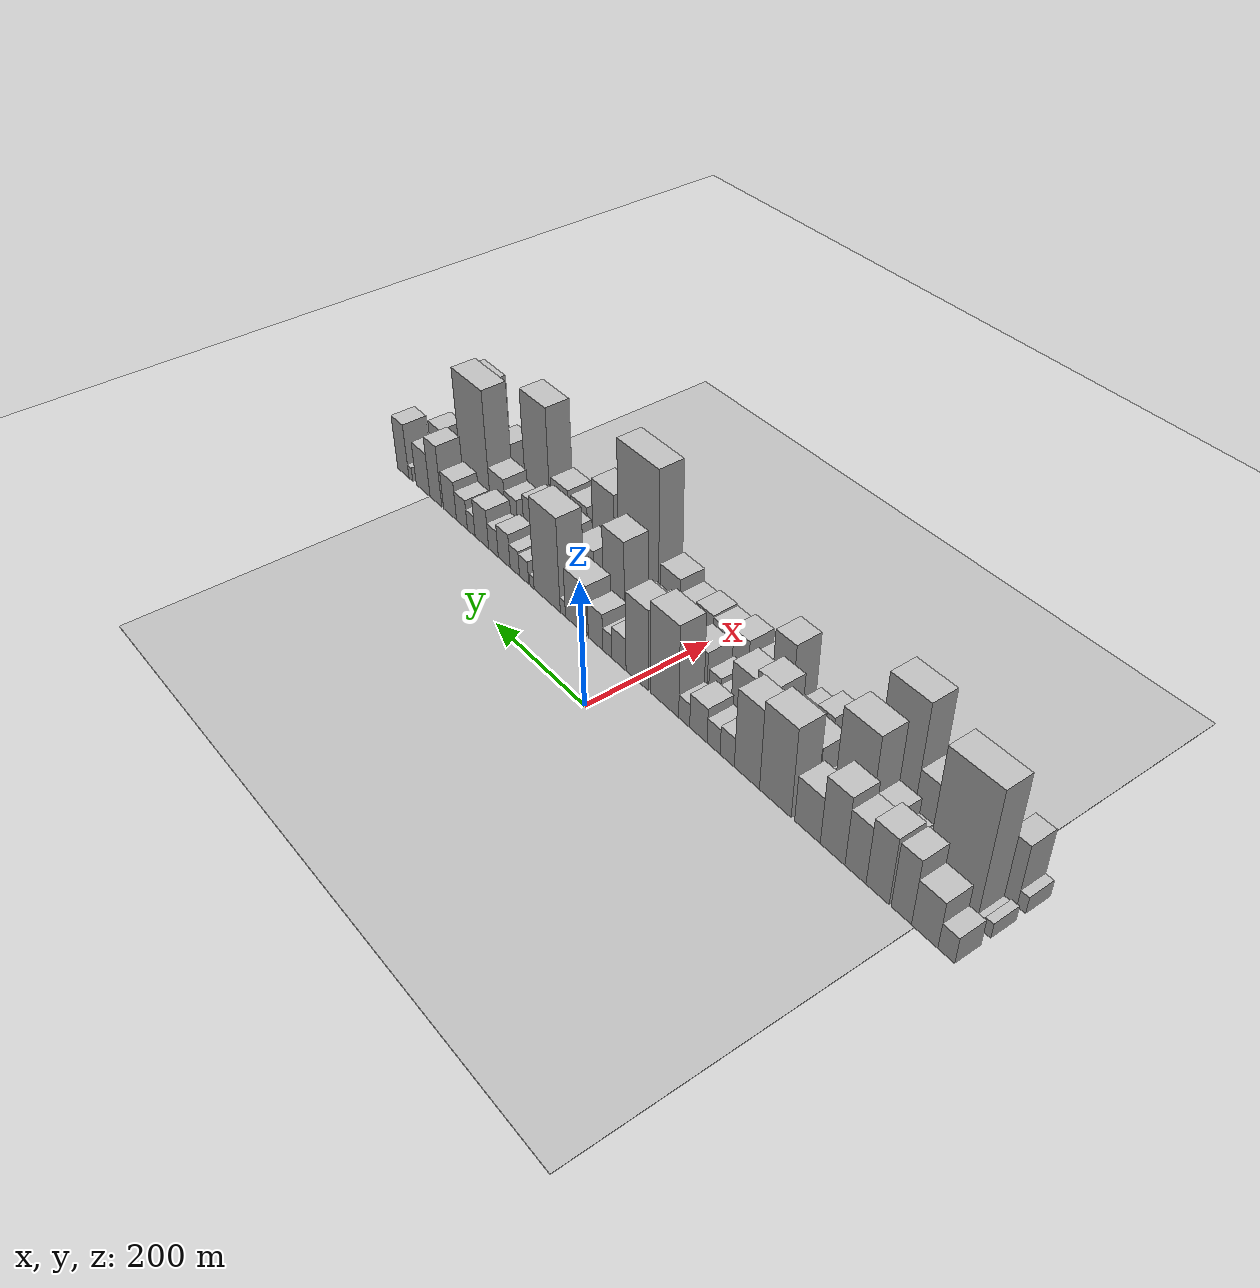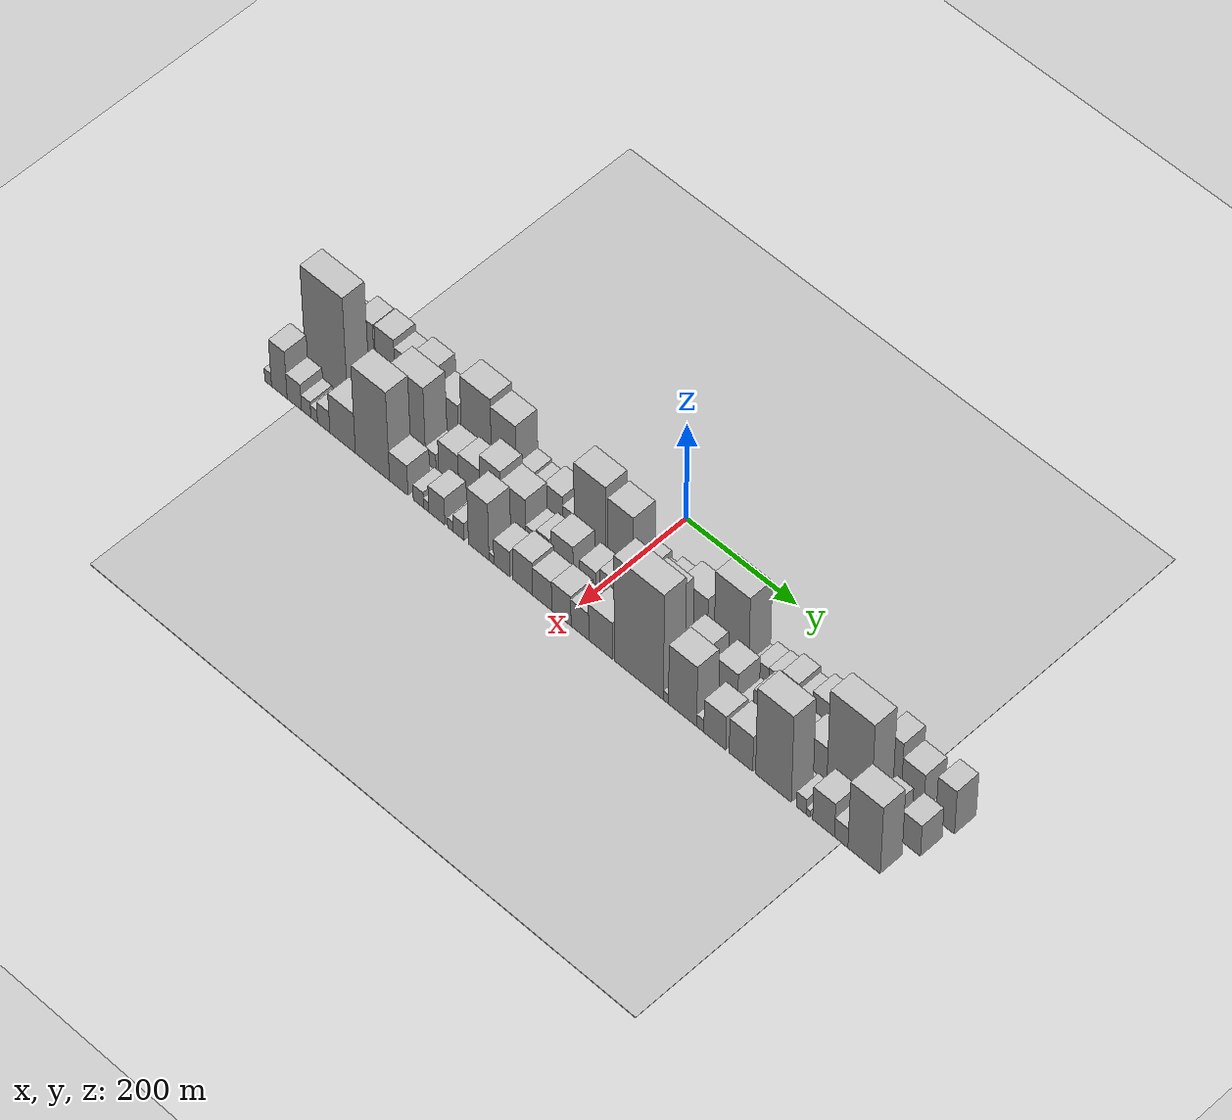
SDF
<?xml version="1.0" encoding="utf-8"?>

<sdf version="1.6">

   <world name="default">

      <gui fullscreen="0">

         <camera name="user_camera">

            <pose>-15 0 4.57585 0 0 0</pose>

            <view_controller>orbit</view_controller>

         </camera>

      </gui>

      <scene>

         <sky>

           <clouds>

             <speed>12</speed>

           </clouds>

         </sky>

         <ambient>0.4 0.4 0.4 1</ambient>

         <background>0.7 0.7 0.7 1</background>

         <shadows>1</shadows>

      </scene>

      <gravity>0 0 -9.8066</gravity>

      <magnetic_field>6e-06 2.3e-05 -4.2e-05</magnetic_field>

      <physics default="0" name="default_physics" type="ode">

         <ode>

            <solver>

               <type>quick</type>

               <iters>10</iters>

               <sor>1.0</sor>

               <use_dynamic_moi_rescaling>0</use_dynamic_moi_rescaling>

            </solver>

            <constraints>

               <cfm>0</cfm>

               <erp>0.2</erp>

               <contact_max_correcting_vel>100</contact_max_correcting_vel>

               <contact_surface_layer>0.001</contact_surface_layer>

            </constraints>

         </ode>

         <max_step_size>0.004</max_step_size>

         <real_time_factor>1</real_time_factor>

         <real_time_update_rate>250</real_time_update_rate>

      </physics>

      <light name="sun" type="directional">

         <cast_shadows>1</cast_shadows>

         <pose>0 0 10 0 0 0</pose>

         <diffuse>0.8 0.8 0.8 1</diffuse>

         <specular>0.2 0.2 0.2 1</specular>

         <attenuation>

            <range>1000</range>

            <constant>0.9</constant>

            <linear>0.01</linear>

            <quadratic>0.001</quadratic>

         </attenuation>

         <direction>-0.5 0.1 -0.9</direction>

      </light>

      <include>

         <name>ground_plane_1</name>

         <uri>model://HANNAS_ground_plane</uri>

         <pose>0 0 0  0 0 0</pose>

      </include>

      <include>

         <name>ground_plane_2</name>

         <uri>model://HANNAS_ground_plane</uri>

         <pose>100 0 0  0 0 0</pose>

      </include>

      <model name="building_1">

         <static>1</static>

         <pose frame="">100.0000 -547.4474 0 0.000000 0.000000 0.000000</pose>

         <link name="link">

            <pose frame="">0 0 21.00 0 0 0</pose>

            <collision name="collision">

               <geometry>

                  <box>

                     <size>40.0000 25.1052 42.0000</size>

                  </box>

               </geometry>

               <max_contacts>10</max_contacts>

               <surface>

                  <contact>

                     <ode/>

                  </contact>

                  <bounce/>

                  <friction>

                     <torsional>

                        <ode/>

                     </torsional>

                     <ode/>

                  </friction>

               </surface>

            </collision>

            <visual name="visual">

               <cast_shadows>0</cast_shadows>

               <geometry>

                  <box>

                     <size>40.0000 25.1052 42.0000</size>

                  </box>

               </geometry>

               <material>

                  <script>

                     <uri>model://HANNAS_wall/materials/scripts</uri>

                     <uri>model://HANNAS_wall/materials/textures</uri>

                     <name>vrc/HANNAS_wall</name>

                  </script>

               </material>

            </visual>

            <self_collide>0</self_collide>

            <enable_wind>0</enable_wind>

            <kinematic>0</kinematic>

         </link>

      </model>

      <model name="building_2">

         <static>1</static>

         <pose frame="">100.0000 -514.9876 0 0.000000 0.000000 0.000000</pose>

         <link name="link">

            <pose frame="">0 0 37.50 0 0 0</pose>

            <collision name="collision">

               <geometry>

                  <box>

                     <size>40.0000 39.8145 75.0000</size>

                  </box>

               </geometry>

               <max_contacts>10</max_contacts>

               <surface>

                  <contact>

                     <ode/>

                  </contact>

                  <bounce/>

                  <friction>

                     <torsional>

                        <ode/>

                     </torsional>

                     <ode/>

                  </friction>

               </surface>

            </collision>

            <visual name="visual">

               <cast_shadows>0</cast_shadows>

               <geometry>

                  <box>

                     <size>40.0000 39.8145 75.0000</size>

                  </box>

               </geometry>

               <material>

                  <script>

                     <uri>model://HANNAS_wall/materials/scripts</uri>

                     <uri>model://HANNAS_wall/materials/textures</uri>

                     <name>vrc/HANNAS_wall</name>

                  </script>

               </material>

            </visual>

            <self_collide>0</self_collide>

            <enable_wind>0</enable_wind>

            <kinematic>0</kinematic>

         </link>

      </model>

      <model name="building_3">

         <static>1</static>

         <pose frame="">100.0000 -479.2793 0 0.000000 0.000000 0.000000</pose>

         <link name="link">

            <pose frame="">0 0 52.50 0 0 0</pose>

            <collision name="collision">

               <geometry>

                  <box>

                     <size>40.0000 31.6019 105.0000</size>

                  </box>

               </geometry>

               <max_contacts>10</max_contacts>

               <surface>

                  <contact>

                     <ode/>

                  </contact>

                  <bounce/>

                  <friction>

                     <torsional>

                        <ode/>

                     </torsional>

                     <ode/>

                  </friction>

               </surface>

            </collision>

            <visual name="visual">

               <cast_shadows>0</cast_shadows>

               <geometry>

                  <box>

                     <size>40.0000 31.6019 105.0000</size>

                  </box>

               </geometry>

               <material>

                  <script>

                     <uri>model://HANNAS_wall/materials/scripts</uri>

                     <uri>model://HANNAS_wall/materials/textures</uri>

                     <name>vrc/HANNAS_wall</name>

                  </script>

               </material>

            </visual>

            <self_collide>0</self_collide>

            <enable_wind>0</enable_wind>

            <kinematic>0</kinematic>

         </link>

      </model>

      <model name="building_4">

         <static>1</static>

         <pose frame="">100.0000 -442.0592 0 0.000000 0.000000 0.000000</pose>

         <link name="link">

            <pose frame="">0 0 54.00 0 0 0</pose>

            <collision name="collision">

               <geometry>

                  <box>

                     <size>40.0000 36.8384 108.0000</size>

                  </box>

               </geometry>

               <max_contacts>10</max_contacts>

               <surface>

                  <contact>

                     <ode/>

                  </contact>

                  <bounce/>

                  <friction>

                     <torsional>

                        <ode/>

                     </torsional>

                     <ode/>

                  </friction>

               </surface>

            </collision>

            <visual name="visual">

               <cast_shadows>0</cast_shadows>

               <geometry>

                  <box>

                     <size>40.0000 36.8384 108.0000</size>

                  </box>

               </geometry>

               <material>

                  <script>

                     <uri>model://HANNAS_wall/materials/scripts</uri>

                     <uri>model://HANNAS_wall/materials/textures</uri>

                     <name>vrc/HANNAS_wall</name>

                  </script>

               </material>

            </visual>

            <self_collide>0</self_collide>

            <enable_wind>0</enable_wind>

            <kinematic>0</kinematic>

         </link>

      </model>

      <model name="building_5">

         <static>1</static>

         <pose frame="">100.0000 -406.5390 0 0.000000 0.000000 0.000000</pose>

         <link name="link">

            <pose frame="">0 0 46.50 0 0 0</pose>

            <collision name="collision">

               <geometry>

                  <box>

                     <size>40.0000 34.2020 93.0000</size>

                  </box>

               </geometry>

               <max_contacts>10</max_contacts>

               <surface>

                  <contact>

                     <ode/>

                  </contact>

                  <bounce/>

                  <friction>

                     <torsional>

                        <ode/>

                     </torsional>

                     <ode/>

                  </friction>

               </surface>

            </collision>

            <visual name="visual">

               <cast_shadows>0</cast_shadows>

               <geometry>

                  <box>

                     <size>40.0000 34.2020 93.0000</size>

                  </box>

               </geometry>

               <material>

                  <script>

                     <uri>model://HANNAS_wall/materials/scripts</uri>

                     <uri>model://HANNAS_wall/materials/textures</uri>

                     <name>vrc/HANNAS_wall</name>

                  </script>

               </material>

            </visual>

            <self_collide>0</self_collide>

            <enable_wind>0</enable_wind>

            <kinematic>0</kinematic>

         </link>

      </model>

      <model name="building_6">

         <static>1</static>

         <pose frame="">100.0000 -368.8271 0 0.000000 0.000000 0.000000</pose>

         <link name="link">

            <pose frame="">0 0 55.50 0 0 0</pose>

            <collision name="collision">

               <geometry>

                  <box>

                     <size>40.0000 41.2217 111.0000</size>

                  </box>

               </geometry>

               <max_contacts>10</max_contacts>

               <surface>

                  <contact>

                     <ode/>

                  </contact>

                  <bounce/>

                  <friction>

                     <torsional>

                        <ode/>

                     </torsional>

                     <ode/>

                  </friction>

               </surface>

            </collision>

            <visual name="visual">

               <cast_shadows>0</cast_shadows>

               <geometry>

                  <box>

                     <size>40.0000 41.2217 111.0000</size>

                  </box>

               </geometry>

               <material>

                  <script>

                     <uri>model://HANNAS_wall/materials/scripts</uri>

                     <uri>model://HANNAS_wall/materials/textures</uri>

                     <name>vrc/HANNAS_wall</name>

                  </script>

               </material>

            </visual>

            <self_collide>0</self_collide>

            <enable_wind>0</enable_wind>

            <kinematic>0</kinematic>

         </link>

      </model>

      <model name="building_7">

         <static>1</static>

         <pose frame="">100.0000 -326.1968 0 0.000000 0.000000 0.000000</pose>

         <link name="link">

            <pose frame="">0 0 37.50 0 0 0</pose>

            <collision name="collision">

               <geometry>

                  <box>

                     <size>40.0000 44.0390 75.0000</size>

                  </box>

               </geometry>

               <max_contacts>10</max_contacts>

               <surface>

                  <contact>

                     <ode/>

                  </contact>

                  <bounce/>

                  <friction>

                     <torsional>

                        <ode/>

                     </torsional>

                     <ode/>

                  </friction>

               </surface>

            </collision>

            <visual name="visual">

               <cast_shadows>0</cast_shadows>

               <geometry>

                  <box>

                     <size>40.0000 44.0390 75.0000</size>

                  </box>

               </geometry>

               <material>

                  <script>

                     <uri>model://HANNAS_wall/materials/scripts</uri>

                     <uri>model://HANNAS_wall/materials/textures</uri>

                     <name>vrc/HANNAS_wall</name>

                  </script>

               </material>

            </visual>

            <self_collide>0</self_collide>

            <enable_wind>0</enable_wind>

            <kinematic>0</kinematic>

         </link>

      </model>

      <model name="building_8">

         <static>1</static>

         <pose frame="">100.0000 -269.9359 0 0.000000 0.000000 0.000000</pose>

         <link name="link">

            <pose frame="">0 0 72.00 0 0 0</pose>

            <collision name="collision">

               <geometry>

                  <box>

                     <size>40.0000 56.4827 144.0000</size>

                  </box>

               </geometry>

               <max_contacts>10</max_contacts>

               <surface>

                  <contact>

                     <ode/>

                  </contact>

                  <bounce/>

                  <friction>

                     <torsional>

                        <ode/>

                     </torsional>

                     <ode/>

                  </friction>

               </surface>

            </collision>

            <visual name="visual">

               <cast_shadows>0</cast_shadows>

               <geometry>

                  <box>

                     <size>40.0000 56.4827 144.0000</size>

                  </box>

               </geometry>

               <material>

                  <script>

                     <uri>model://HANNAS_wall/materials/scripts</uri>

                     <uri>model://HANNAS_wall/materials/textures</uri>

                     <name>vrc/HANNAS_wall</name>

                  </script>

               </material>

            </visual>

            <self_collide>0</self_collide>

            <enable_wind>0</enable_wind>

            <kinematic>0</kinematic>

         </link>

      </model>

      <model name="building_9">

         <static>1</static>

         <pose frame="">100.0000 -218.4961 0 0.000000 0.000000 0.000000</pose>

         <link name="link">

            <pose frame="">0 0 64.50 0 0 0</pose>

            <collision name="collision">

               <geometry>

                  <box>

                     <size>40.0000 46.3969 129.0000</size>

                  </box>

               </geometry>

               <max_contacts>10</max_contacts>

               <surface>

                  <contact>

                     <ode/>

                  </contact>

                  <bounce/>

                  <friction>

                     <torsional>

                        <ode/>

                     </torsional>

                     <ode/>

                  </friction>

               </surface>

            </collision>

            <visual name="visual">

               <cast_shadows>0</cast_shadows>

               <geometry>

                  <box>

                     <size>40.0000 46.3969 129.0000</size>

                  </box>

               </geometry>

               <material>

                  <script>

                     <uri>model://HANNAS_wall/materials/scripts</uri>

                     <uri>model://HANNAS_wall/materials/textures</uri>

                     <name>vrc/HANNAS_wall</name>

                  </script>

               </material>

            </visual>

            <self_collide>0</self_collide>

            <enable_wind>0</enable_wind>

            <kinematic>0</kinematic>

         </link>

      </model>

      <model name="building_10">

         <static>1</static>

         <pose frame="">100.0000 -181.8941 0 0.000000 0.000000 0.000000</pose>

         <link name="link">

            <pose frame="">0 0 24.00 0 0 0</pose>

            <collision name="collision">

               <geometry>

                  <box>

                     <size>40.0000 26.8072 48.0000</size>

                  </box>

               </geometry>

               <max_contacts>10</max_contacts>

               <surface>

                  <contact>

                     <ode/>

                  </contact>

                  <bounce/>

                  <friction>

                     <torsional>

                        <ode/>

                     </torsional>

                     <ode/>

                  </friction>

               </surface>

            </collision>

            <visual name="visual">

               <cast_shadows>0</cast_shadows>

               <geometry>

                  <box>

                     <size>40.0000 26.8072 48.0000</size>

                  </box>

               </geometry>

               <material>

                  <script>

                     <uri>model://HANNAS_wall/materials/scripts</uri>

                     <uri>model://HANNAS_wall/materials/textures</uri>

                     <name>vrc/HANNAS_wall</name>

                  </script>

               </material>

            </visual>

            <self_collide>0</self_collide>

            <enable_wind>0</enable_wind>

            <kinematic>0</kinematic>

         </link>

      </model>

      <model name="building_11">

         <static>1</static>

         <pose frame="">100.0000 -156.0569 0 0.000000 0.000000 0.000000</pose>

         <link name="link">

            <pose frame="">0 0 21.00 0 0 0</pose>

            <collision name="collision">

               <geometry>

                  <box>

                     <size>40.0000 24.8672 42.0000</size>

                  </box>

               </geometry>

               <max_contacts>10</max_contacts>

               <surface>

                  <contact>

                     <ode/>

                  </contact>

                  <bounce/>

                  <friction>

                     <torsional>

                        <ode/>

                     </torsional>

                     <ode/>

                  </friction>

               </surface>

            </collision>

            <visual name="visual">

               <cast_shadows>0</cast_shadows>

               <geometry>

                  <box>

                     <size>40.0000 24.8672 42.0000</size>

                  </box>

               </geometry>

               <material>

                  <script>

                     <uri>model://HANNAS_wall/materials/scripts</uri>

                     <uri>model://HANNAS_wall/materials/textures</uri>

                     <name>vrc/HANNAS_wall</name>

                  </script>

               </material>

            </visual>

            <self_collide>0</self_collide>

            <enable_wind>0</enable_wind>

            <kinematic>0</kinematic>

         </link>

      </model>

      <model name="building_12">

         <static>1</static>

         <pose frame="">100.0000 -126.6801 0 0.000000 0.000000 0.000000</pose>

         <link name="link">

            <pose frame="">0 0 28.50 0 0 0</pose>

            <collision name="collision">

               <geometry>

                  <box>

                     <size>40.0000 33.8864 57.0000</size>

                  </box>

               </geometry>

               <max_contacts>10</max_contacts>

               <surface>

                  <contact>

                     <ode/>

                  </contact>

                  <bounce/>

                  <friction>

                     <torsional>

                        <ode/>

                     </torsional>

                     <ode/>

                  </friction>

               </surface>

            </collision>

            <visual name="visual">

               <cast_shadows>0</cast_shadows>

               <geometry>

                  <box>

                     <size>40.0000 33.8864 57.0000</size>

                  </box>

               </geometry>

               <material>

                  <script>

                     <uri>model://HANNAS_wall/materials/scripts</uri>

                     <uri>model://HANNAS_wall/materials/textures</uri>

                     <name>vrc/HANNAS_wall</name>

                  </script>

               </material>

            </visual>

            <self_collide>0</self_collide>

            <enable_wind>0</enable_wind>

            <kinematic>0</kinematic>

         </link>

      </model>

      <model name="building_13">

         <static>1</static>

         <pose frame="">100.0000 -98.7835 0 0.000000 0.000000 0.000000</pose>

         <link name="link">

            <pose frame="">0 0 19.50 0 0 0</pose>

            <collision name="collision">

               <geometry>

                  <box>

                     <size>40.0000 21.9067 39.0000</size>

                  </box>

               </geometry>

               <max_contacts>10</max_contacts>

               <surface>

                  <contact>

                     <ode/>

                  </contact>

                  <bounce/>

                  <friction>

                     <torsional>

                        <ode/>

                     </torsional>

                     <ode/>

                  </friction>

               </surface>

            </collision>

            <visual name="visual">

               <cast_shadows>0</cast_shadows>

               <geometry>

                  <box>

                     <size>40.0000 21.9067 39.0000</size>

                  </box>

               </geometry>

               <material>

                  <script>

                     <uri>model://HANNAS_wall/materials/scripts</uri>

                     <uri>model://HANNAS_wall/materials/textures</uri>

                     <name>vrc/HANNAS_wall</name>

                  </script>

               </material>

            </visual>

            <self_collide>0</self_collide>

            <enable_wind>0</enable_wind>

            <kinematic>0</kinematic>

         </link>

      </model>

      <model name="building_14">

         <static>1</static>

         <pose frame="">100.0000 -58.8187 0 0.000000 0.000000 0.000000</pose>

         <link name="link">

            <pose frame="">0 0 75.00 0 0 0</pose>

            <collision name="collision">

               <geometry>

                  <box>

                     <size>40.0000 58.0228 150.0000</size>

                  </box>

               </geometry>

               <max_contacts>10</max_contacts>

               <surface>

                  <contact>

                     <ode/>

                  </contact>

                  <bounce/>

                  <friction>

                     <torsional>

                        <ode/>

                     </torsional>

                     <ode/>

                  </friction>

               </surface>

            </collision>

            <visual name="visual">

               <cast_shadows>0</cast_shadows>

               <geometry>

                  <box>

                     <size>40.0000 58.0228 150.0000</size>

                  </box>

               </geometry>

               <material>

                  <script>

                     <uri>model://HANNAS_wall/materials/scripts</uri>

                     <uri>model://HANNAS_wall/materials/textures</uri>

                     <name>vrc/HANNAS_wall</name>

                  </script>

               </material>

            </visual>

            <self_collide>0</self_collide>

            <enable_wind>0</enable_wind>

            <kinematic>0</kinematic>

         </link>

      </model>

      <model name="building_15">

         <static>1</static>

         <pose frame="">100.0000 -2.3847 0 0.000000 0.000000 0.000000</pose>

         <link name="link">

            <pose frame="">0 0 66.00 0 0 0</pose>

            <collision name="collision">

               <geometry>

                  <box>

                     <size>40.0000 46.8452 132.0000</size>

                  </box>

               </geometry>

               <max_contacts>10</max_contacts>

               <surface>

                  <contact>

                     <ode/>

                  </contact>

                  <bounce/>

                  <friction>

                     <torsional>

                        <ode/>

                     </torsional>

                     <ode/>

                  </friction>

               </surface>

            </collision>

            <visual name="visual">

               <cast_shadows>0</cast_shadows>

               <geometry>

                  <box>

                     <size>40.0000 46.8452 132.0000</size>

                  </box>

               </geometry>

               <material>

                  <script>

                     <uri>model://HANNAS_wall/materials/scripts</uri>

                     <uri>model://HANNAS_wall/materials/textures</uri>

                     <name>vrc/HANNAS_wall</name>

                  </script>

               </material>

            </visual>

            <self_collide>0</self_collide>

            <enable_wind>0</enable_wind>

            <kinematic>0</kinematic>

         </link>

      </model>

      <model name="building_16">

         <static>1</static>

         <pose frame="">100.0000 36.3263 0 0.000000 0.000000 0.000000</pose>

         <link name="link">

            <pose frame="">0 0 27.00 0 0 0</pose>

            <collision name="collision">

               <geometry>

                  <box>

                     <size>40.0000 30.5769 54.0000</size>

                  </box>

               </geometry>

               <max_contacts>10</max_contacts>

               <surface>

                  <contact>

                     <ode/>

                  </contact>

                  <bounce/>

                  <friction>

                     <torsional>

                        <ode/>

                     </torsional>

                     <ode/>

                  </friction>

               </surface>

            </collision>

            <visual name="visual">

               <cast_shadows>0</cast_shadows>

               <geometry>

                  <box>

                     <size>40.0000 30.5769 54.0000</size>

                  </box>

               </geometry>

               <material>

                  <script>

                     <uri>model://HANNAS_wall/materials/scripts</uri>

                     <uri>model://HANNAS_wall/materials/textures</uri>

                     <name>vrc/HANNAS_wall</name>

                  </script>

               </material>

            </visual>

            <self_collide>0</self_collide>

            <enable_wind>0</enable_wind>

            <kinematic>0</kinematic>

         </link>

      </model>

      <model name="building_17">

         <static>1</static>

         <pose frame="">100.0000 61.5209 0 0.000000 0.000000 0.000000</pose>

         <link name="link">

            <pose frame="">0 0 19.50 0 0 0</pose>

            <collision name="collision">

               <geometry>

                  <box>

                     <size>40.0000 19.8122 39.0000</size>

                  </box>

               </geometry>

               <max_contacts>10</max_contacts>

               <surface>

                  <contact>

                     <ode/>

                  </contact>

                  <bounce/>

                  <friction>

                     <torsional>

                        <ode/>

                     </torsional>

                     <ode/>

                  </friction>

               </surface>

            </collision>

            <visual name="visual">

               <cast_shadows>0</cast_shadows>

               <geometry>

                  <box>

                     <size>40.0000 19.8122 39.0000</size>

                  </box>

               </geometry>

               <material>

                  <script>

                     <uri>model://HANNAS_wall/materials/scripts</uri>

                     <uri>model://HANNAS_wall/materials/textures</uri>

                     <name>vrc/HANNAS_wall</name>

                  </script>

               </material>

            </visual>

            <self_collide>0</self_collide>

            <enable_wind>0</enable_wind>

            <kinematic>0</kinematic>

         </link>

      </model>

      <model name="building_18">

         <static>1</static>

         <pose frame="">100.0000 87.4213 0 0.000000 0.000000 0.000000</pose>

         <link name="link">

            <pose frame="">0 0 30.00 0 0 0</pose>

            <collision name="collision">

               <geometry>

                  <box>

                     <size>40.0000 31.9886 60.0000</size>

                  </box>

               </geometry>

               <max_contacts>10</max_contacts>

               <surface>

                  <contact>

                     <ode/>

                  </contact>

                  <bounce/>

                  <friction>

                     <torsional>

                        <ode/>

                     </torsional>

                     <ode/>

                  </friction>

               </surface>

            </collision>

            <visual name="visual">

               <cast_shadows>0</cast_shadows>

               <geometry>

                  <box>

                     <size>40.0000 31.9886 60.0000</size>

                  </box>

               </geometry>

               <material>

                  <script>

                     <uri>model://HANNAS_wall/materials/scripts</uri>

                     <uri>model://HANNAS_wall/materials/textures</uri>

                     <name>vrc/HANNAS_wall</name>

                  </script>

               </material>

            </visual>

            <self_collide>0</self_collide>

            <enable_wind>0</enable_wind>

            <kinematic>0</kinematic>

         </link>

      </model>

      <model name="building_19">

         <static>1</static>

         <pose frame="">100.0000 131.0985 0 0.000000 0.000000 0.000000</pose>

         <link name="link">

            <pose frame="">0 0 42.00 0 0 0</pose>

            <collision name="collision">

               <geometry>

                  <box>

                     <size>40.0000 49.3658 84.0000</size>

                  </box>

               </geometry>

               <max_contacts>10</max_contacts>

               <surface>

                  <contact>

                     <ode/>

                  </contact>

                  <bounce/>

                  <friction>

                     <torsional>

                        <ode/>

                     </torsional>

                     <ode/>

                  </friction>

               </surface>

            </collision>

            <visual name="visual">

               <cast_shadows>0</cast_shadows>

               <geometry>

                  <box>

                     <size>40.0000 49.3658 84.0000</size>

                  </box>

               </geometry>

               <material>

                  <script>

                     <uri>model://HANNAS_wall/materials/scripts</uri>

                     <uri>model://HANNAS_wall/materials/textures</uri>

                     <name>vrc/HANNAS_wall</name>

                  </script>

               </material>

            </visual>

            <self_collide>0</self_collide>

            <enable_wind>0</enable_wind>

            <kinematic>0</kinematic>

         </link>

      </model>

      <model name="building_20">

         <static>1</static>

         <pose frame="">100.0000 161.7609 0 0.000000 0.000000 0.000000</pose>

         <link name="link">

            <pose frame="">0 0 13.50 0 0 0</pose>

            <collision name="collision">

               <geometry>

                  <box>

                     <size>40.0000 11.9590 27.0000</size>

                  </box>

               </geometry>

               <max_contacts>10</max_contacts>

               <surface>

                  <contact>

                     <ode/>

                  </contact>

                  <bounce/>

                  <friction>

                     <torsional>

                        <ode/>

                     </torsional>

                     <ode/>

                  </friction>

               </surface>

            </collision>

            <visual name="visual">

               <cast_shadows>0</cast_shadows>

               <geometry>

                  <box>

                     <size>40.0000 11.9590 27.0000</size>

                  </box>

               </geometry>

               <material>

                  <script>

                     <uri>model://HANNAS_wall/materials/scripts</uri>

                     <uri>model://HANNAS_wall/materials/textures</uri>

                     <name>vrc/HANNAS_wall</name>

                  </script>

               </material>

            </visual>

            <self_collide>0</self_collide>

            <enable_wind>0</enable_wind>

            <kinematic>0</kinematic>

         </link>

      </model>

      <model name="building_21">

         <static>1</static>

         <pose frame="">100.0000 198.7092 0 0.000000 0.000000 0.000000</pose>

         <link name="link">

            <pose frame="">0 0 78.00 0 0 0</pose>

            <collision name="collision">

               <geometry>

                  <box>

                     <size>40.0000 61.9377 156.0000</size>

                  </box>

               </geometry>

               <max_contacts>10</max_contacts>

               <surface>

                  <contact>

                     <ode/>

                  </contact>

                  <bounce/>

                  <friction>

                     <torsional>

                        <ode/>

                     </torsional>

                     <ode/>

                  </friction>

               </surface>

            </collision>

            <visual name="visual">

               <cast_shadows>0</cast_shadows>

               <geometry>

                  <box>

                     <size>40.0000 61.9377 156.0000</size>

                  </box>

               </geometry>

               <material>

                  <script>

                     <uri>model://HANNAS_wall/materials/scripts</uri>

                     <uri>model://HANNAS_wall/materials/textures</uri>

                     <name>vrc/HANNAS_wall</name>

                  </script>

               </material>

            </visual>

            <self_collide>0</self_collide>

            <enable_wind>0</enable_wind>

            <kinematic>0</kinematic>

         </link>

      </model>

      <model name="building_22">

         <static>1</static>

         <pose frame="">100.0000 234.6944 0 0.000000 0.000000 0.000000</pose>

         <link name="link">

            <pose frame="">0 0 10.50 0 0 0</pose>

            <collision name="collision">

               <geometry>

                  <box>

                     <size>40.0000 10.0326 21.0000</size>

                  </box>

               </geometry>

               <max_contacts>10</max_contacts>

               <surface>

                  <contact>

                     <ode/>

                  </contact>

                  <bounce/>

                  <friction>

                     <torsional>

                        <ode/>

                     </torsional>

                     <ode/>

                  </friction>

               </surface>

            </collision>

            <visual name="visual">

               <cast_shadows>0</cast_shadows>

               <geometry>

                  <box>

                     <size>40.0000 10.0326 21.0000</size>

                  </box>

               </geometry>

               <material>

                  <script>

                     <uri>model://HANNAS_wall/materials/scripts</uri>

                     <uri>model://HANNAS_wall/materials/textures</uri>

                     <name>vrc/HANNAS_wall</name>

                  </script>

               </material>

            </visual>

            <self_collide>0</self_collide>

            <enable_wind>0</enable_wind>

            <kinematic>0</kinematic>

         </link>

      </model>

      <model name="building_23">

         <static>1</static>

         <pose frame="">100.0000 253.9902 0 0.000000 0.000000 0.000000</pose>

         <link name="link">

            <pose frame="">0 0 19.50 0 0 0</pose>

            <collision name="collision">

               <geometry>

                  <box>

                     <size>40.0000 22.5590 39.0000</size>

                  </box>

               </geometry>

               <max_contacts>10</max_contacts>

               <surface>

                  <contact>

                     <ode/>

                  </contact>

                  <bounce/>

                  <friction>

                     <torsional>

                        <ode/>

                     </torsional>

                     <ode/>

                  </friction>

               </surface>

            </collision>

            <visual name="visual">

               <cast_shadows>0</cast_shadows>

               <geometry>

                  <box>

                     <size>40.0000 22.5590 39.0000</size>

                  </box>

               </geometry>

               <material>

                  <script>

                     <uri>model://HANNAS_wall/materials/scripts</uri>

                     <uri>model://HANNAS_wall/materials/textures</uri>

                     <name>vrc/HANNAS_wall</name>

                  </script>

               </material>

            </visual>

            <self_collide>0</self_collide>

            <enable_wind>0</enable_wind>

            <kinematic>0</kinematic>

         </link>

      </model>

      <model name="building_24">

         <static>1</static>

         <pose frame="">100.0000 276.7857 0 0.000000 0.000000 0.000000</pose>

         <link name="link">

            <pose frame="">0 0 21.00 0 0 0</pose>

            <collision name="collision">

               <geometry>

                  <box>

                     <size>40.0000 23.0320 42.0000</size>

                  </box>

               </geometry>

               <max_contacts>10</max_contacts>

               <surface>

                  <contact>

                     <ode/>

                  </contact>

                  <bounce/>

                  <friction>

                     <torsional>

                        <ode/>

                     </torsional>

                     <ode/>

                  </friction>

               </surface>

            </collision>

            <visual name="visual">

               <cast_shadows>0</cast_shadows>

               <geometry>

                  <box>

                     <size>40.0000 23.0320 42.0000</size>

                  </box>

               </geometry>

               <material>

                  <script>

                     <uri>model://HANNAS_wall/materials/scripts</uri>

                     <uri>model://HANNAS_wall/materials/textures</uri>

                     <name>vrc/HANNAS_wall</name>

                  </script>

               </material>

            </visual>

            <self_collide>0</self_collide>

            <enable_wind>0</enable_wind>

            <kinematic>0</kinematic>

         </link>

      </model>

      <model name="building_25">

         <static>1</static>

         <pose frame="">100.0000 303.2867 0 0.000000 0.000000 0.000000</pose>

         <link name="link">

            <pose frame="">0 0 28.50 0 0 0</pose>

            <collision name="collision">

               <geometry>

                  <box>

                     <size>40.0000 29.9701 57.0000</size>

                  </box>

               </geometry>

               <max_contacts>10</max_contacts>

               <surface>

                  <contact>

                     <ode/>

                  </contact>

                  <bounce/>

                  <friction>

                     <torsional>

                        <ode/>

                     </torsional>

                     <ode/>

                  </friction>

               </surface>

            </collision>

            <visual name="visual">

               <cast_shadows>0</cast_shadows>

               <geometry>

                  <box>

                     <size>40.0000 29.9701 57.0000</size>

                  </box>

               </geometry>

               <material>

                  <script>

                     <uri>model://HANNAS_wall/materials/scripts</uri>

                     <uri>model://HANNAS_wall/materials/textures</uri>

                     <name>vrc/HANNAS_wall</name>

                  </script>

               </material>

            </visual>

            <self_collide>0</self_collide>

            <enable_wind>0</enable_wind>

            <kinematic>0</kinematic>

         </link>

      </model>

      <model name="building_26">

         <static>1</static>

         <pose frame="">100.0000 330.5248 0 0.000000 0.000000 0.000000</pose>

         <link name="link">

            <pose frame="">0 0 22.50 0 0 0</pose>

            <collision name="collision">

               <geometry>

                  <box>

                     <size>40.0000 24.5061 45.0000</size>

                  </box>

               </geometry>

               <max_contacts>10</max_contacts>

               <surface>

                  <contact>

                     <ode/>

                  </contact>

                  <bounce/>

                  <friction>

                     <torsional>

                        <ode/>

                     </torsional>

                     <ode/>

                  </friction>

               </surface>

            </collision>

            <visual name="visual">

               <cast_shadows>0</cast_shadows>

               <geometry>

                  <box>

                     <size>40.0000 24.5061 45.0000</size>

                  </box>

               </geometry>

               <material>

                  <script>

                     <uri>model://HANNAS_wall/materials/scripts</uri>

                     <uri>model://HANNAS_wall/materials/textures</uri>

                     <name>vrc/HANNAS_wall</name>

                  </script>

               </material>

            </visual>

            <self_collide>0</self_collide>

            <enable_wind>0</enable_wind>

            <kinematic>0</kinematic>

         </link>

      </model>

      <model name="building_27">

         <static>1</static>

         <pose frame="">100.0000 360.3790 0 0.000000 0.000000 0.000000</pose>

         <link name="link">

            <pose frame="">0 0 33.00 0 0 0</pose>

            <collision name="collision">

               <geometry>

                  <box>

                     <size>40.0000 35.2023 66.0000</size>

                  </box>

               </geometry>

               <max_contacts>10</max_contacts>

               <surface>

                  <contact>

                     <ode/>

                  </contact>

                  <bounce/>

                  <friction>

                     <torsional>

                        <ode/>

                     </torsional>

                     <ode/>

                  </friction>

               </surface>

            </collision>

            <visual name="visual">

               <cast_shadows>0</cast_shadows>

               <geometry>

                  <box>

                     <size>40.0000 35.2023 66.0000</size>

                  </box>

               </geometry>

               <material>

                  <script>

                     <uri>model://HANNAS_wall/materials/scripts</uri>

                     <uri>model://HANNAS_wall/materials/textures</uri>

                     <name>vrc/HANNAS_wall</name>

                  </script>

               </material>

            </visual>

            <self_collide>0</self_collide>

            <enable_wind>0</enable_wind>

            <kinematic>0</kinematic>

         </link>

      </model>

      <model name="building_28">

         <static>1</static>

         <pose frame="">100.0000 388.1173 0 0.000000 0.000000 0.000000</pose>

         <link name="link">

            <pose frame="">0 0 18.00 0 0 0</pose>

            <collision name="collision">

               <geometry>

                  <box>

                     <size>40.0000 20.2742 36.0000</size>

                  </box>

               </geometry>

               <max_contacts>10</max_contacts>

               <surface>

                  <contact>

                     <ode/>

                  </contact>

                  <bounce/>

                  <friction>

                     <torsional>

                        <ode/>

                     </torsional>

                     <ode/>

                  </friction>

               </surface>

            </collision>

            <visual name="visual">

               <cast_shadows>0</cast_shadows>

               <geometry>

                  <box>

                     <size>40.0000 20.2742 36.0000</size>

                  </box>

               </geometry>

               <material>

                  <script>

                     <uri>model://HANNAS_wall/materials/scripts</uri>

                     <uri>model://HANNAS_wall/materials/textures</uri>

                     <name>vrc/HANNAS_wall</name>

                  </script>

               </material>

            </visual>

            <self_collide>0</self_collide>

            <enable_wind>0</enable_wind>

            <kinematic>0</kinematic>

         </link>

      </model>

      <model name="building_29">

         <static>1</static>

         <pose frame="">100.0000 412.7300 0 0.000000 0.000000 0.000000</pose>

         <link name="link">

            <pose frame="">0 0 25.50 0 0 0</pose>

            <collision name="collision">

               <geometry>

                  <box>

                     <size>40.0000 28.9512 51.0000</size>

                  </box>

               </geometry>

               <max_contacts>10</max_contacts>

               <surface>

                  <contact>

                     <ode/>

                  </contact>

                  <bounce/>

                  <friction>

                     <torsional>

                        <ode/>

                     </torsional>

                     <ode/>

                  </friction>

               </surface>

            </collision>

            <visual name="visual">

               <cast_shadows>0</cast_shadows>

               <geometry>

                  <box>

                     <size>40.0000 28.9512 51.0000</size>

                  </box>

               </geometry>

               <material>

                  <script>

                     <uri>model://HANNAS_wall/materials/scripts</uri>

                     <uri>model://HANNAS_wall/materials/textures</uri>

                     <name>vrc/HANNAS_wall</name>

                  </script>

               </material>

            </visual>

            <self_collide>0</self_collide>

            <enable_wind>0</enable_wind>

            <kinematic>0</kinematic>

         </link>

      </model>

      <model name="building_30">

         <static>1</static>

         <pose frame="">100.0000 444.6950 0 0.000000 0.000000 0.000000</pose>

         <link name="link">

            <pose frame="">0 0 33.00 0 0 0</pose>

            <collision name="collision">

               <geometry>

                  <box>

                     <size>40.0000 34.9790 66.0000</size>

                  </box>

               </geometry>

               <max_contacts>10</max_contacts>

               <surface>

                  <contact>

                     <ode/>

                  </contact>

                  <bounce/>

                  <friction>

                     <torsional>

                        <ode/>

                     </torsional>

                     <ode/>

                  </friction>

               </surface>

            </collision>

            <visual name="visual">

               <cast_shadows>0</cast_shadows>

               <geometry>

                  <box>

                     <size>40.0000 34.9790 66.0000</size>

                  </box>

               </geometry>

               <material>

                  <script>

                     <uri>model://HANNAS_wall/materials/scripts</uri>

                     <uri>model://HANNAS_wall/materials/textures</uri>

                     <name>vrc/HANNAS_wall</name>

                  </script>

               </material>

            </visual>

            <self_collide>0</self_collide>

            <enable_wind>0</enable_wind>

            <kinematic>0</kinematic>

         </link>

      </model>

      <model name="building_31">

         <static>1</static>

         <pose frame="">100.0000 483.4821 0 0.000000 0.000000 0.000000</pose>

         <link name="link">

            <pose frame="">0 0 52.50 0 0 0</pose>

            <collision name="collision">

               <geometry>

                  <box>

                     <size>40.0000 32.5952 105.0000</size>

                  </box>

               </geometry>

               <max_contacts>10</max_contacts>

               <surface>

                  <contact>

                     <ode/>

                  </contact>

                  <bounce/>

                  <friction>

                     <torsional>

                        <ode/>

                     </torsional>

                     <ode/>

                  </friction>

               </surface>

            </collision>

            <visual name="visual">

               <cast_shadows>0</cast_shadows>

               <geometry>

                  <box>

                     <size>40.0000 32.5952 105.0000</size>

                  </box>

               </geometry>

               <material>

                  <script>

                     <uri>model://HANNAS_wall/materials/scripts</uri>

                     <uri>model://HANNAS_wall/materials/textures</uri>

                     <name>vrc/HANNAS_wall</name>

                  </script>

               </material>

            </visual>

            <self_collide>0</self_collide>

            <enable_wind>0</enable_wind>

            <kinematic>0</kinematic>

         </link>

      </model>

      <model name="building_32">

         <static>1</static>

         <pose frame="">100.0000 519.2023 0 0.000000 0.000000 0.000000</pose>

         <link name="link">

            <pose frame="">0 0 37.50 0 0 0</pose>

            <collision name="collision">

               <geometry>

                  <box>

                     <size>40.0000 38.8451 75.0000</size>

                  </box>

               </geometry>

               <max_contacts>10</max_contacts>

               <surface>

                  <contact>

                     <ode/>

                  </contact>

                  <bounce/>

                  <friction>

                     <torsional>

                        <ode/>

                     </torsional>

                     <ode/>

                  </friction>

               </surface>

            </collision>

            <visual name="visual">

               <cast_shadows>0</cast_shadows>

               <geometry>

                  <box>

                     <size>40.0000 38.8451 75.0000</size>

                  </box>

               </geometry>

               <material>

                  <script>

                     <uri>model://HANNAS_wall/materials/scripts</uri>

                     <uri>model://HANNAS_wall/materials/textures</uri>

                     <name>vrc/HANNAS_wall</name>

                  </script>

               </material>

            </visual>

            <self_collide>0</self_collide>

            <enable_wind>0</enable_wind>

            <kinematic>0</kinematic>

         </link>

      </model>

      <model name="building_33">

         <static>1</static>

         <pose frame="">100.0000 554.0830 0 0.000000 0.000000 0.000000</pose>

         <link name="link">

            <pose frame="">0 0 12.00 0 0 0</pose>

            <collision name="collision">

               <geometry>

                  <box>

                     <size>40.0000 10.9162 24.0000</size>

                  </box>

               </geometry>

               <max_contacts>10</max_contacts>

               <surface>

                  <contact>

                     <ode/>

                  </contact>

                  <bounce/>

                  <friction>

                     <torsional>

                        <ode/>

                     </torsional>

                     <ode/>

                  </friction>

               </surface>

            </collision>

            <visual name="visual">

               <cast_shadows>0</cast_shadows>

               <geometry>

                  <box>

                     <size>40.0000 10.9162 24.0000</size>

                  </box>

               </geometry>

               <material>

                  <script>

                     <uri>model://HANNAS_wall/materials/scripts</uri>

                     <uri>model://HANNAS_wall/materials/textures</uri>

                     <name>vrc/HANNAS_wall</name>

                  </script>

               </material>

            </visual>

            <self_collide>0</self_collide>

            <enable_wind>0</enable_wind>

            <kinematic>0</kinematic>

         </link>

      </model>

      <model name="building_34">

         <static>1</static>

         <pose frame="">100.0000 575.7398 0 0.000000 0.000000 0.000000</pose>

         <link name="link">

            <pose frame="">0 0 46.50 0 0 0</pose>

            <collision name="collision">

               <geometry>

                  <box>

                     <size>40.0000 32.3975 93.0000</size>

                  </box>

               </geometry>

               <max_contacts>10</max_contacts>

               <surface>

                  <contact>

                     <ode/>

                  </contact>

                  <bounce/>

                  <friction>

                     <torsional>

                        <ode/>

                     </torsional>

                     <ode/>

                  </friction>

               </surface>

            </collision>

            <visual name="visual">

               <cast_shadows>0</cast_shadows>

               <geometry>

                  <box>

                     <size>40.0000 32.3975 93.0000</size>

                  </box>

               </geometry>

               <material>

                  <script>

                     <uri>model://HANNAS_wall/materials/scripts</uri>

                     <uri>model://HANNAS_wall/materials/textures</uri>

                     <name>vrc/HANNAS_wall</name>

                  </script>

               </material>

            </visual>

            <self_collide>0</self_collide>

            <enable_wind>0</enable_wind>

            <kinematic>0</kinematic>

         </link>

      </model>

      <model name="building_35">

         <static>1</static>

         <pose frame="">155.0000 -554.0229 0 0.000000 0.000000 0.000000</pose>

         <link name="link">

            <pose frame="">0 0 12.00 0 0 0</pose>

            <collision name="collision">

               <geometry>

                  <box>

                     <size>40.0000 11.9541 24.0000</size>

                  </box>

               </geometry>

               <max_contacts>10</max_contacts>

               <surface>

                  <contact>

                     <ode/>

                  </contact>

                  <bounce/>

                  <friction>

                     <torsional>

                        <ode/>

                     </torsional>

                     <ode/>

                  </friction>

               </surface>

            </collision>

            <visual name="visual">

               <cast_shadows>0</cast_shadows>

               <geometry>

                  <box>

                     <size>40.0000 11.9541 24.0000</size>

                  </box>

               </geometry>

               <material>

                  <script>

                     <uri>model://HANNAS_wall/materials/scripts</uri>

                     <uri>model://HANNAS_wall/materials/textures</uri>

                     <name>vrc/HANNAS_wall</name>

                  </script>

               </material>

            </visual>

            <self_collide>0</self_collide>

            <enable_wind>0</enable_wind>

            <kinematic>0</kinematic>

         </link>

      </model>

      <model name="building_36">

         <static>1</static>

         <pose frame="">155.0000 -543.2162 0 0.000000 0.000000 0.000000</pose>

         <link name="link">

            <pose frame="">0 0 10.50 0 0 0</pose>

            <collision name="collision">

               <geometry>

                  <box>

                     <size>40.0000 9.6593 21.0000</size>

                  </box>

               </geometry>

               <max_contacts>10</max_contacts>

               <surface>

                  <contact>

                     <ode/>

                  </contact>

                  <bounce/>

                  <friction>

                     <torsional>

                        <ode/>

                     </torsional>

                     <ode/>

                  </friction>

               </surface>

            </collision>

            <visual name="visual">

               <cast_shadows>0</cast_shadows>

               <geometry>

                  <box>

                     <size>40.0000 9.6593 21.0000</size>

                  </box>

               </geometry>

               <material>

                  <script>

                     <uri>model://HANNAS_wall/materials/scripts</uri>

                     <uri>model://HANNAS_wall/materials/textures</uri>

                     <name>vrc/HANNAS_wall</name>

                  </script>

               </material>

            </visual>

            <self_collide>0</self_collide>

            <enable_wind>0</enable_wind>

            <kinematic>0</kinematic>

         </link>

      </model>

      <model name="building_37">

         <static>1</static>

         <pose frame="">155.0000 -498.4545 0 0.000000 0.000000 0.000000</pose>

         <link name="link">

            <pose frame="">0 0 106.50 0 0 0</pose>

            <collision name="collision">

               <geometry>

                  <box>

                     <size>40.0000 79.8641 213.0000</size>

                  </box>

               </geometry>

               <max_contacts>10</max_contacts>

               <surface>

                  <contact>

                     <ode/>

                  </contact>

                  <bounce/>

                  <friction>

                     <torsional>

                        <ode/>

                     </torsional>

                     <ode/>

                  </friction>

               </surface>

            </collision>

            <visual name="visual">

               <cast_shadows>0</cast_shadows>

               <geometry>

                  <box>

                     <size>40.0000 79.8641 213.0000</size>

                  </box>

               </geometry>

               <material>

                  <script>

                     <uri>model://HANNAS_wall/materials/scripts</uri>

                     <uri>model://HANNAS_wall/materials/textures</uri>

                     <name>vrc/HANNAS_wall</name>

                  </script>

               </material>

            </visual>

            <self_collide>0</self_collide>

            <enable_wind>0</enable_wind>

            <kinematic>0</kinematic>

         </link>

      </model>

      <model name="building_38">

         <static>1</static>

         <pose frame="">155.0000 -450.0620 0 0.000000 0.000000 0.000000</pose>

         <link name="link">

            <pose frame="">0 0 7.50 0 0 0</pose>

            <collision name="collision">

               <geometry>

                  <box>

                     <size>40.0000 6.9209 15.0000</size>

                  </box>

               </geometry>

               <max_contacts>10</max_contacts>

               <surface>

                  <contact>

                     <ode/>

                  </contact>

                  <bounce/>

                  <friction>

                     <torsional>

                        <ode/>

                     </torsional>

                     <ode/>

                  </friction>

               </surface>

            </collision>

            <visual name="visual">

               <cast_shadows>0</cast_shadows>

               <geometry>

                  <box>

                     <size>40.0000 6.9209 15.0000</size>

                  </box>

               </geometry>

               <material>

                  <script>

                     <uri>model://HANNAS_wall/materials/scripts</uri>

                     <uri>model://HANNAS_wall/materials/textures</uri>

                     <name>vrc/HANNAS_wall</name>

                  </script>

               </material>

            </visual>

            <self_collide>0</self_collide>

            <enable_wind>0</enable_wind>

            <kinematic>0</kinematic>

         </link>

      </model>

      <model name="building_39">

         <static>1</static>

         <pose frame="">155.0000 -437.4602 0 0.000000 0.000000 0.000000</pose>

         <link name="link">

            <pose frame="">0 0 18.00 0 0 0</pose>

            <collision name="collision">

               <geometry>

                  <box>

                     <size>40.0000 18.2828 36.0000</size>

                  </box>

               </geometry>

               <max_contacts>10</max_contacts>

               <surface>

                  <contact>

                     <ode/>

                  </contact>

                  <bounce/>

                  <friction>

                     <torsional>

                        <ode/>

                     </torsional>

                     <ode/>

                  </friction>

               </surface>

            </collision>

            <visual name="visual">

               <cast_shadows>0</cast_shadows>

               <geometry>

                  <box>

                     <size>40.0000 18.2828 36.0000</size>

                  </box>

               </geometry>

               <material>

                  <script>

                     <uri>model://HANNAS_wall/materials/scripts</uri>

                     <uri>model://HANNAS_wall/materials/textures</uri>

                     <name>vrc/HANNAS_wall</name>

                  </script>

               </material>

            </visual>

            <self_collide>0</self_collide>

            <enable_wind>0</enable_wind>

            <kinematic>0</kinematic>

         </link>

      </model>

      <model name="building_40">

         <static>1</static>

         <pose frame="">155.0000 -417.2199 0 0.000000 0.000000 0.000000</pose>

         <link name="link">

            <pose frame="">0 0 19.50 0 0 0</pose>

            <collision name="collision">

               <geometry>

                  <box>

                     <size>40.0000 22.1979 39.0000</size>

                  </box>

               </geometry>

               <max_contacts>10</max_contacts>

               <surface>

                  <contact>

                     <ode/>

                  </contact>

                  <bounce/>

                  <friction>

                     <torsional>

                        <ode/>

                     </torsional>

                     <ode/>

                  </friction>

               </surface>

            </collision>

            <visual name="visual">

               <cast_shadows>0</cast_shadows>

               <geometry>

                  <box>

                     <size>40.0000 22.1979 39.0000</size>

                  </box>

               </geometry>

               <material>

                  <script>

                     <uri>model://HANNAS_wall/materials/scripts</uri>

                     <uri>model://HANNAS_wall/materials/textures</uri>

                     <name>vrc/HANNAS_wall</name>

                  </script>

               </material>

            </visual>

            <self_collide>0</self_collide>

            <enable_wind>0</enable_wind>

            <kinematic>0</kinematic>

         </link>

      </model>

      <model name="building_41">

         <static>1</static>

         <pose frame="">155.0000 -388.3180 0 0.000000 0.000000 0.000000</pose>

         <link name="link">

            <pose frame="">0 0 31.50 0 0 0</pose>

            <collision name="collision">

               <geometry>

                  <box>

                     <size>40.0000 35.6058 63.0000</size>

                  </box>

               </geometry>

               <max_contacts>10</max_contacts>

               <surface>

                  <contact>

                     <ode/>

                  </contact>

                  <bounce/>

                  <friction>

                     <torsional>

                        <ode/>

                     </torsional>

                     <ode/>

                  </friction>

               </surface>

            </collision>

            <visual name="visual">

               <cast_shadows>0</cast_shadows>

               <geometry>

                  <box>

                     <size>40.0000 35.6058 63.0000</size>

                  </box>

               </geometry>

               <material>

                  <script>

                     <uri>model://HANNAS_wall/materials/scripts</uri>

                     <uri>model://HANNAS_wall/materials/textures</uri>

                     <name>vrc/HANNAS_wall</name>

                  </script>

               </material>

            </visual>

            <self_collide>0</self_collide>

            <enable_wind>0</enable_wind>

            <kinematic>0</kinematic>

         </link>

      </model>

      <model name="building_42">

         <static>1</static>

         <pose frame="">155.0000 -340.1591 0 0.000000 0.000000 0.000000</pose>

         <link name="link">

            <pose frame="">0 0 78.00 0 0 0</pose>

            <collision name="collision">

               <geometry>

                  <box>

                     <size>40.0000 60.7120 156.0000</size>

                  </box>

               </geometry>

               <max_contacts>10</max_contacts>

               <surface>

                  <contact>

                     <ode/>

                  </contact>

                  <bounce/>

                  <friction>

                     <torsional>

                        <ode/>

                     </torsional>

                     <ode/>

                  </friction>

               </surface>

            </collision>

            <visual name="visual">

               <cast_shadows>0</cast_shadows>

               <geometry>

                  <box>

                     <size>40.0000 60.7120 156.0000</size>

                  </box>

               </geometry>

               <material>

                  <script>

                     <uri>model://HANNAS_wall/materials/scripts</uri>

                     <uri>model://HANNAS_wall/materials/textures</uri>

                     <name>vrc/HANNAS_wall</name>

                  </script>

               </material>

            </visual>

            <self_collide>0</self_collide>

            <enable_wind>0</enable_wind>

            <kinematic>0</kinematic>

         </link>

      </model>

      <model name="building_43">

         <static>1</static>

         <pose frame="">155.0000 -300.0281 0 0.000000 0.000000 0.000000</pose>

         <link name="link">

            <pose frame="">0 0 16.50 0 0 0</pose>

            <collision name="collision">

               <geometry>

                  <box>

                     <size>40.0000 19.5500 33.0000</size>

                  </box>

               </geometry>

               <max_contacts>10</max_contacts>

               <surface>

                  <contact>

                     <ode/>

                  </contact>

                  <bounce/>

                  <friction>

                     <torsional>

                        <ode/>

                     </torsional>

                     <ode/>

                  </friction>

               </surface>

            </collision>

            <visual name="visual">

               <cast_shadows>0</cast_shadows>

               <geometry>

                  <box>

                     <size>40.0000 19.5500 33.0000</size>

                  </box>

               </geometry>

               <material>

                  <script>

                     <uri>model://HANNAS_wall/materials/scripts</uri>

                     <uri>model://HANNAS_wall/materials/textures</uri>

                     <name>vrc/HANNAS_wall</name>

                  </script>

               </material>

            </visual>

            <self_collide>0</self_collide>

            <enable_wind>0</enable_wind>

            <kinematic>0</kinematic>

         </link>

      </model>

      <model name="building_44">

         <static>1</static>

         <pose frame="">155.0000 -266.4066 0 0.000000 0.000000 0.000000</pose>

         <link name="link">

            <pose frame="">0 0 34.50 0 0 0</pose>

            <collision name="collision">

               <geometry>

                  <box>

                     <size>40.0000 37.6930 69.0000</size>

                  </box>

               </geometry>

               <max_contacts>10</max_contacts>

               <surface>

                  <contact>

                     <ode/>

                  </contact>

                  <bounce/>

                  <friction>

                     <torsional>

                        <ode/>

                     </torsional>

                     <ode/>

                  </friction>

               </surface>

            </collision>

            <visual name="visual">

               <cast_shadows>0</cast_shadows>

               <geometry>

                  <box>

                     <size>40.0000 37.6930 69.0000</size>

                  </box>

               </geometry>

               <material>

                  <script>

                     <uri>model://HANNAS_wall/materials/scripts</uri>

                     <uri>model://HANNAS_wall/materials/textures</uri>

                     <name>vrc/HANNAS_wall</name>

                  </script>

               </material>

            </visual>

            <self_collide>0</self_collide>

            <enable_wind>0</enable_wind>

            <kinematic>0</kinematic>

         </link>

      </model>

      <model name="building_45">

         <static>1</static>

         <pose frame="">155.0000 -227.3587 0 0.000000 0.000000 0.000000</pose>

         <link name="link">

            <pose frame="">0 0 37.50 0 0 0</pose>

            <collision name="collision">

               <geometry>

                  <box>

                     <size>40.0000 40.4029 75.0000</size>

                  </box>

               </geometry>

               <max_contacts>10</max_contacts>

               <surface>

                  <contact>

                     <ode/>

                  </contact>

                  <bounce/>

                  <friction>

                     <torsional>

                        <ode/>

                     </torsional>

                     <ode/>

                  </friction>

               </surface>

            </collision>

            <visual name="visual">

               <cast_shadows>0</cast_shadows>

               <geometry>

                  <box>

                     <size>40.0000 40.4029 75.0000</size>

                  </box>

               </geometry>

               <material>

                  <script>

                     <uri>model://HANNAS_wall/materials/scripts</uri>

                     <uri>model://HANNAS_wall/materials/textures</uri>

                     <name>vrc/HANNAS_wall</name>

                  </script>

               </material>

            </visual>

            <self_collide>0</self_collide>

            <enable_wind>0</enable_wind>

            <kinematic>0</kinematic>

         </link>

      </model>

      <model name="building_46">

         <static>1</static>

         <pose frame="">155.0000 -187.5203 0 0.000000 0.000000 0.000000</pose>

         <link name="link">

            <pose frame="">0 0 54.00 0 0 0</pose>

            <collision name="collision">

               <geometry>

                  <box>

                     <size>40.0000 39.2738 108.0000</size>

                  </box>

               </geometry>

               <max_contacts>10</max_contacts>

               <surface>

                  <contact>

                     <ode/>

                  </contact>

                  <bounce/>

                  <friction>

                     <torsional>

                        <ode/>

                     </torsional>

                     <ode/>

                  </friction>

               </surface>

            </collision>

            <visual name="visual">

               <cast_shadows>0</cast_shadows>

               <geometry>

                  <box>

                     <size>40.0000 39.2738 108.0000</size>

                  </box>

               </geometry>

               <material>

                  <script>

                     <uri>model://HANNAS_wall/materials/scripts</uri>

                     <uri>model://HANNAS_wall/materials/textures</uri>

                     <name>vrc/HANNAS_wall</name>

                  </script>

               </material>

            </visual>

            <self_collide>0</self_collide>

            <enable_wind>0</enable_wind>

            <kinematic>0</kinematic>

         </link>

      </model>

      <model name="building_47">

         <static>1</static>

         <pose frame="">155.0000 -145.2305 0 0.000000 0.000000 0.000000</pose>

         <link name="link">

            <pose frame="">0 0 45.00 0 0 0</pose>

            <collision name="collision">

               <geometry>

                  <box>

                     <size>40.0000 45.3057 90.0000</size>

                  </box>

               </geometry>

               <max_contacts>10</max_contacts>

               <surface>

                  <contact>

                     <ode/>

                  </contact>

                  <bounce/>

                  <friction>

                     <torsional>

                        <ode/>

                     </torsional>

                     <ode/>

                  </friction>

               </surface>

            </collision>

            <visual name="visual">

               <cast_shadows>0</cast_shadows>

               <geometry>

                  <box>

                     <size>40.0000 45.3057 90.0000</size>

                  </box>

               </geometry>

               <material>

                  <script>

                     <uri>model://HANNAS_wall/materials/scripts</uri>

                     <uri>model://HANNAS_wall/materials/textures</uri>

                     <name>vrc/HANNAS_wall</name>

                  </script>

               </material>

            </visual>

            <self_collide>0</self_collide>

            <enable_wind>0</enable_wind>

            <kinematic>0</kinematic>

         </link>

      </model>

      <model name="building_48">

         <static>1</static>

         <pose frame="">155.0000 -112.5735 0 0.000000 0.000000 0.000000</pose>

         <link name="link">

            <pose frame="">0 0 18.00 0 0 0</pose>

            <collision name="collision">

               <geometry>

                  <box>

                     <size>40.0000 20.0084 36.0000</size>

                  </box>

               </geometry>

               <max_contacts>10</max_contacts>

               <surface>

                  <contact>

                     <ode/>

                  </contact>

                  <bounce/>

                  <friction>

                     <torsional>

                        <ode/>

                     </torsional>

                     <ode/>

                  </friction>

               </surface>

            </collision>

            <visual name="visual">

               <cast_shadows>0</cast_shadows>

               <geometry>

                  <box>

                     <size>40.0000 20.0084 36.0000</size>

                  </box>

               </geometry>

               <material>

                  <script>

                     <uri>model://HANNAS_wall/materials/scripts</uri>

                     <uri>model://HANNAS_wall/materials/textures</uri>

                     <name>vrc/HANNAS_wall</name>

                  </script>

               </material>

            </visual>

            <self_collide>0</self_collide>

            <enable_wind>0</enable_wind>

            <kinematic>0</kinematic>

         </link>

      </model>

      <model name="building_49">

         <static>1</static>

         <pose frame="">155.0000 -90.6602 0 0.000000 0.000000 0.000000</pose>

         <link name="link">

            <pose frame="">0 0 22.50 0 0 0</pose>

            <collision name="collision">

               <geometry>

                  <box>

                     <size>40.0000 23.8183 45.0000</size>

                  </box>

               </geometry>

               <max_contacts>10</max_contacts>

               <surface>

                  <contact>

                     <ode/>

                  </contact>

                  <bounce/>

                  <friction>

                     <torsional>

                        <ode/>

                     </torsional>

                     <ode/>

                  </friction>

               </surface>

            </collision>

            <visual name="visual">

               <cast_shadows>0</cast_shadows>

               <geometry>

                  <box>

                     <size>40.0000 23.8183 45.0000</size>

                  </box>

               </geometry>

               <material>

                  <script>

                     <uri>model://HANNAS_wall/materials/scripts</uri>

                     <uri>model://HANNAS_wall/materials/textures</uri>

                     <name>vrc/HANNAS_wall</name>

                  </script>

               </material>

            </visual>

            <self_collide>0</self_collide>

            <enable_wind>0</enable_wind>

            <kinematic>0</kinematic>

         </link>

      </model>

      <model name="building_50">

         <static>1</static>

         <pose frame="">155.0000 -55.3497 0 0.000000 0.000000 0.000000</pose>

         <link name="link">

            <pose frame="">0 0 34.50 0 0 0</pose>

            <collision name="collision">

               <geometry>

                  <box>

                     <size>40.0000 40.8027 69.0000</size>

                  </box>

               </geometry>

               <max_contacts>10</max_contacts>

               <surface>

                  <contact>

                     <ode/>

                  </contact>

                  <bounce/>

                  <friction>

                     <torsional>

                        <ode/>

                     </torsional>

                     <ode/>

                  </friction>

               </surface>

            </collision>

            <visual name="visual">

               <cast_shadows>0</cast_shadows>

               <geometry>

                  <box>

                     <size>40.0000 40.8027 69.0000</size>

                  </box>

               </geometry>

               <material>

                  <script>

                     <uri>model://HANNAS_wall/materials/scripts</uri>

                     <uri>model://HANNAS_wall/materials/textures</uri>

                     <name>vrc/HANNAS_wall</name>

                  </script>

               </material>

            </visual>

            <self_collide>0</self_collide>

            <enable_wind>0</enable_wind>

            <kinematic>0</kinematic>

         </link>

      </model>

      <model name="building_51">

         <static>1</static>

         <pose frame="">155.0000 -30.5072 0 0.000000 0.000000 0.000000</pose>

         <link name="link">

            <pose frame="">0 0 9.00 0 0 0</pose>

            <collision name="collision">

               <geometry>

                  <box>

                     <size>40.0000 8.8824 18.0000</size>

                  </box>

               </geometry>

               <max_contacts>10</max_contacts>

               <surface>

                  <contact>

                     <ode/>

                  </contact>

                  <bounce/>

                  <friction>

                     <torsional>

                        <ode/>

                     </torsional>

                     <ode/>

                  </friction>

               </surface>

            </collision>

            <visual name="visual">

               <cast_shadows>0</cast_shadows>

               <geometry>

                  <box>

                     <size>40.0000 8.8824 18.0000</size>

                  </box>

               </geometry>

               <material>

                  <script>

                     <uri>model://HANNAS_wall/materials/scripts</uri>

                     <uri>model://HANNAS_wall/materials/textures</uri>

                     <name>vrc/HANNAS_wall</name>

                  </script>

               </material>

            </visual>

            <self_collide>0</self_collide>

            <enable_wind>0</enable_wind>

            <kinematic>0</kinematic>

         </link>

      </model>

      <model name="building_52">

         <static>1</static>

         <pose frame="">155.0000 -7.8343 0 0.000000 0.000000 0.000000</pose>

         <link name="link">

            <pose frame="">0 0 27.00 0 0 0</pose>

            <collision name="collision">

               <geometry>

                  <box>

                     <size>40.0000 30.4632 54.0000</size>

                  </box>

               </geometry>

               <max_contacts>10</max_contacts>

               <surface>

                  <contact>

                     <ode/>

                  </contact>

                  <bounce/>

                  <friction>

                     <torsional>

                        <ode/>

                     </torsional>

                     <ode/>

                  </friction>

               </surface>

            </collision>

            <visual name="visual">

               <cast_shadows>0</cast_shadows>

               <geometry>

                  <box>

                     <size>40.0000 30.4632 54.0000</size>

                  </box>

               </geometry>

               <material>

                  <script>

                     <uri>model://HANNAS_wall/materials/scripts</uri>

                     <uri>model://HANNAS_wall/materials/textures</uri>

                     <name>vrc/HANNAS_wall</name>

                  </script>

               </material>

            </visual>

            <self_collide>0</self_collide>

            <enable_wind>0</enable_wind>

            <kinematic>0</kinematic>

         </link>

      </model>

      <model name="building_53">

         <static>1</static>

         <pose frame="">155.0000 10.7663 0 0.000000 0.000000 0.000000</pose>

         <link name="link">

            <pose frame="">0 0 7.50 0 0 0</pose>

            <collision name="collision">

               <geometry>

                  <box>

                     <size>40.0000 6.7381 15.0000</size>

                  </box>

               </geometry>

               <max_contacts>10</max_contacts>

               <surface>

                  <contact>

                     <ode/>

                  </contact>

                  <bounce/>

                  <friction>

                     <torsional>

                        <ode/>

                     </torsional>

                     <ode/>

                  </friction>

               </surface>

            </collision>

            <visual name="visual">

               <cast_shadows>0</cast_shadows>

               <geometry>

                  <box>

                     <size>40.0000 6.7381 15.0000</size>

                  </box>

               </geometry>

               <material>

                  <script>

                     <uri>model://HANNAS_wall/materials/scripts</uri>

                     <uri>model://HANNAS_wall/materials/textures</uri>

                     <name>vrc/HANNAS_wall</name>

                  </script>

               </material>

            </visual>

            <self_collide>0</self_collide>

            <enable_wind>0</enable_wind>

            <kinematic>0</kinematic>

         </link>

      </model>

      <model name="building_54">

         <static>1</static>

         <pose frame="">155.0000 31.9293 0 0.000000 0.000000 0.000000</pose>

         <link name="link">

            <pose frame="">0 0 34.50 0 0 0</pose>

            <collision name="collision">

               <geometry>

                  <box>

                     <size>40.0000 35.5880 69.0000</size>

                  </box>

               </geometry>

               <max_contacts>10</max_contacts>

               <surface>

                  <contact>

                     <ode/>

                  </contact>

                  <bounce/>

                  <friction>

                     <torsional>

                        <ode/>

                     </torsional>

                     <ode/>

                  </friction>

               </surface>

            </collision>

            <visual name="visual">

               <cast_shadows>0</cast_shadows>

               <geometry>

                  <box>

                     <size>40.0000 35.5880 69.0000</size>

                  </box>

               </geometry>

               <material>

                  <script>

                     <uri>model://HANNAS_wall/materials/scripts</uri>

                     <uri>model://HANNAS_wall/materials/textures</uri>

                     <name>vrc/HANNAS_wall</name>

                  </script>

               </material>

            </visual>

            <self_collide>0</self_collide>

            <enable_wind>0</enable_wind>

            <kinematic>0</kinematic>

         </link>

      </model>

      <model name="building_55">

         <static>1</static>

         <pose frame="">155.0000 66.1047 0 0.000000 0.000000 0.000000</pose>

         <link name="link">

            <pose frame="">0 0 31.50 0 0 0</pose>

            <collision name="collision">

               <geometry>

                  <box>

                     <size>40.0000 32.7628 63.0000</size>

                  </box>

               </geometry>

               <max_contacts>10</max_contacts>

               <surface>

                  <contact>

                     <ode/>

                  </contact>

                  <bounce/>

                  <friction>

                     <torsional>

                        <ode/>

                     </torsional>

                     <ode/>

                  </friction>

               </surface>

            </collision>

            <visual name="visual">

               <cast_shadows>0</cast_shadows>

               <geometry>

                  <box>

                     <size>40.0000 32.7628 63.0000</size>

                  </box>

               </geometry>

               <material>

                  <script>

                     <uri>model://HANNAS_wall/materials/scripts</uri>

                     <uri>model://HANNAS_wall/materials/textures</uri>

                     <name>vrc/HANNAS_wall</name>

                  </script>

               </material>

            </visual>

            <self_collide>0</self_collide>

            <enable_wind>0</enable_wind>

            <kinematic>0</kinematic>

         </link>

      </model>

      <model name="building_56">

         <static>1</static>

         <pose frame="">155.0000 92.9295 0 0.000000 0.000000 0.000000</pose>

         <link name="link">

            <pose frame="">0 0 10.50 0 0 0</pose>

            <collision name="collision">

               <geometry>

                  <box>

                     <size>40.0000 8.8868 21.0000</size>

                  </box>

               </geometry>

               <max_contacts>10</max_contacts>

               <surface>

                  <contact>

                     <ode/>

                  </contact>

                  <bounce/>

                  <friction>

                     <torsional>

                        <ode/>

                     </torsional>

                     <ode/>

                  </friction>

               </surface>

            </collision>

            <visual name="visual">

               <cast_shadows>0</cast_shadows>

               <geometry>

                  <box>

                     <size>40.0000 8.8868 21.0000</size>

                  </box>

               </geometry>

               <material>

                  <script>

                     <uri>model://HANNAS_wall/materials/scripts</uri>

                     <uri>model://HANNAS_wall/materials/textures</uri>

                     <name>vrc/HANNAS_wall</name>

                  </script>

               </material>

            </visual>

            <self_collide>0</self_collide>

            <enable_wind>0</enable_wind>

            <kinematic>0</kinematic>

         </link>

      </model>

      <model name="building_57">

         <static>1</static>

         <pose frame="">155.0000 120.9628 0 0.000000 0.000000 0.000000</pose>

         <link name="link">

            <pose frame="">0 0 67.50 0 0 0</pose>

            <collision name="collision">

               <geometry>

                  <box>

                     <size>40.0000 47.1796 135.0000</size>

                  </box>

               </geometry>

               <max_contacts>10</max_contacts>

               <surface>

                  <contact>

                     <ode/>

                  </contact>

                  <bounce/>

                  <friction>

                     <torsional>

                        <ode/>

                     </torsional>

                     <ode/>

                  </friction>

               </surface>

            </collision>

            <visual name="visual">

               <cast_shadows>0</cast_shadows>

               <geometry>

                  <box>

                     <size>40.0000 47.1796 135.0000</size>

                  </box>

               </geometry>

               <material>

                  <script>

                     <uri>model://HANNAS_wall/materials/scripts</uri>

                     <uri>model://HANNAS_wall/materials/textures</uri>

                     <name>vrc/HANNAS_wall</name>

                  </script>

               </material>

            </visual>

            <self_collide>0</self_collide>

            <enable_wind>0</enable_wind>

            <kinematic>0</kinematic>

         </link>

      </model>

      <model name="building_58">

         <static>1</static>

         <pose frame="">155.0000 155.0983 0 0.000000 0.000000 0.000000</pose>

         <link name="link">

            <pose frame="">0 0 18.00 0 0 0</pose>

            <collision name="collision">

               <geometry>

                  <box>

                     <size>40.0000 21.0915 36.0000</size>

                  </box>

               </geometry>

               <max_contacts>10</max_contacts>

               <surface>

                  <contact>

                     <ode/>

                  </contact>

                  <bounce/>

                  <friction>

                     <torsional>

                        <ode/>

                     </torsional>

                     <ode/>

                  </friction>

               </surface>

            </collision>

            <visual name="visual">

               <cast_shadows>0</cast_shadows>

               <geometry>

                  <box>

                     <size>40.0000 21.0915 36.0000</size>

                  </box>

               </geometry>

               <material>

                  <script>

                     <uri>model://HANNAS_wall/materials/scripts</uri>

                     <uri>model://HANNAS_wall/materials/textures</uri>

                     <name>vrc/HANNAS_wall</name>

                  </script>

               </material>

            </visual>

            <self_collide>0</self_collide>

            <enable_wind>0</enable_wind>

            <kinematic>0</kinematic>

         </link>

      </model>

      <model name="building_59">

         <static>1</static>

         <pose frame="">155.0000 186.5194 0 0.000000 0.000000 0.000000</pose>

         <link name="link">

            <pose frame="">0 0 39.00 0 0 0</pose>

            <collision name="collision">

               <geometry>

                  <box>

                     <size>40.0000 41.7508 78.0000</size>

                  </box>

               </geometry>

               <max_contacts>10</max_contacts>

               <surface>

                  <contact>

                     <ode/>

                  </contact>

                  <bounce/>

                  <friction>

                     <torsional>

                        <ode/>

                     </torsional>

                     <ode/>

                  </friction>

               </surface>

            </collision>

            <visual name="visual">

               <cast_shadows>0</cast_shadows>

               <geometry>

                  <box>

                     <size>40.0000 41.7508 78.0000</size>

                  </box>

               </geometry>

               <material>

                  <script>

                     <uri>model://HANNAS_wall/materials/scripts</uri>

                     <uri>model://HANNAS_wall/materials/textures</uri>

                     <name>vrc/HANNAS_wall</name>

                  </script>

               </material>

            </visual>

            <self_collide>0</self_collide>

            <enable_wind>0</enable_wind>

            <kinematic>0</kinematic>

         </link>

      </model>

      <model name="building_60">

         <static>1</static>

         <pose frame="">155.0000 215.4919 0 0.000000 0.000000 0.000000</pose>

         <link name="link">

            <pose frame="">0 0 15.00 0 0 0</pose>

            <collision name="collision">

               <geometry>

                  <box>

                     <size>40.0000 16.1943 30.0000</size>

                  </box>

               </geometry>

               <max_contacts>10</max_contacts>

               <surface>

                  <contact>

                     <ode/>

                  </contact>

                  <bounce/>

                  <friction>

                     <torsional>

                        <ode/>

                     </torsional>

                     <ode/>

                  </friction>

               </surface>

            </collision>

            <visual name="visual">

               <cast_shadows>0</cast_shadows>

               <geometry>

                  <box>

                     <size>40.0000 16.1943 30.0000</size>

                  </box>

               </geometry>

               <material>

                  <script>

                     <uri>model://HANNAS_wall/materials/scripts</uri>

                     <uri>model://HANNAS_wall/materials/textures</uri>

                     <name>vrc/HANNAS_wall</name>

                  </script>

               </material>

            </visual>

            <self_collide>0</self_collide>

            <enable_wind>0</enable_wind>

            <kinematic>0</kinematic>

         </link>

      </model>

      <model name="building_61">

         <static>1</static>

         <pose frame="">155.0000 243.4715 0 0.000000 0.000000 0.000000</pose>

         <link name="link">

            <pose frame="">0 0 39.00 0 0 0</pose>

            <collision name="collision">

               <geometry>

                  <box>

                     <size>40.0000 39.7648 78.0000</size>

                  </box>

               </geometry>

               <max_contacts>10</max_contacts>

               <surface>

                  <contact>

                     <ode/>

                  </contact>

                  <bounce/>

                  <friction>

                     <torsional>

                        <ode/>

                     </torsional>

                     <ode/>

                  </friction>

               </surface>

            </collision>

            <visual name="visual">

               <cast_shadows>0</cast_shadows>

               <geometry>

                  <box>

                     <size>40.0000 39.7648 78.0000</size>

                  </box>

               </geometry>

               <material>

                  <script>

                     <uri>model://HANNAS_wall/materials/scripts</uri>

                     <uri>model://HANNAS_wall/materials/textures</uri>

                     <name>vrc/HANNAS_wall</name>

                  </script>

               </material>

            </visual>

            <self_collide>0</self_collide>

            <enable_wind>0</enable_wind>

            <kinematic>0</kinematic>

         </link>

      </model>

      <model name="building_62">

         <static>1</static>

         <pose frame="">155.0000 276.2190 0 0.000000 0.000000 0.000000</pose>

         <link name="link">

            <pose frame="">0 0 18.00 0 0 0</pose>

            <collision name="collision">

               <geometry>

                  <box>

                     <size>40.0000 19.7302 36.0000</size>

                  </box>

               </geometry>

               <max_contacts>10</max_contacts>

               <surface>

                  <contact>

                     <ode/>

                  </contact>

                  <bounce/>

                  <friction>

                     <torsional>

                        <ode/>

                     </torsional>

                     <ode/>

                  </friction>

               </surface>

            </collision>

            <visual name="visual">

               <cast_shadows>0</cast_shadows>

               <geometry>

                  <box>

                     <size>40.0000 19.7302 36.0000</size>

                  </box>

               </geometry>

               <material>

                  <script>

                     <uri>model://HANNAS_wall/materials/scripts</uri>

                     <uri>model://HANNAS_wall/materials/textures</uri>

                     <name>vrc/HANNAS_wall</name>

                  </script>

               </material>

            </visual>

            <self_collide>0</self_collide>

            <enable_wind>0</enable_wind>

            <kinematic>0</kinematic>

         </link>

      </model>

      <model name="building_63">

         <static>1</static>

         <pose frame="">155.0000 312.7297 0 0.000000 0.000000 0.000000</pose>

         <link name="link">

            <pose frame="">0 0 37.50 0 0 0</pose>

            <collision name="collision">

               <geometry>

                  <box>

                     <size>40.0000 43.2913 75.0000</size>

                  </box>

               </geometry>

               <max_contacts>10</max_contacts>

               <surface>

                  <contact>

                     <ode/>

                  </contact>

                  <bounce/>

                  <friction>

                     <torsional>

                        <ode/>

                     </torsional>

                     <ode/>

                  </friction>

               </surface>

            </collision>

            <visual name="visual">

               <cast_shadows>0</cast_shadows>

               <geometry>

                  <box>

                     <size>40.0000 43.2913 75.0000</size>

                  </box>

               </geometry>

               <material>

                  <script>

                     <uri>model://HANNAS_wall/materials/scripts</uri>

                     <uri>model://HANNAS_wall/materials/textures</uri>

                     <name>vrc/HANNAS_wall</name>

                  </script>

               </material>

            </visual>

            <self_collide>0</self_collide>

            <enable_wind>0</enable_wind>

            <kinematic>0</kinematic>

         </link>

      </model>

      <model name="building_64">

         <static>1</static>

         <pose frame="">155.0000 346.9850 0 0.000000 0.000000 0.000000</pose>

         <link name="link">

            <pose frame="">0 0 7.50 0 0 0</pose>

            <collision name="collision">

               <geometry>

                  <box>

                     <size>40.0000 7.2193 15.0000</size>

                  </box>

               </geometry>

               <max_contacts>10</max_contacts>

               <surface>

                  <contact>

                     <ode/>

                  </contact>

                  <bounce/>

                  <friction>

                     <torsional>

                        <ode/>

                     </torsional>

                     <ode/>

                  </friction>

               </surface>

            </collision>

            <visual name="visual">

               <cast_shadows>0</cast_shadows>

               <geometry>

                  <box>

                     <size>40.0000 7.2193 15.0000</size>

                  </box>

               </geometry>

               <material>

                  <script>

                     <uri>model://HANNAS_wall/materials/scripts</uri>

                     <uri>model://HANNAS_wall/materials/textures</uri>

                     <name>vrc/HANNAS_wall</name>

                  </script>

               </material>

            </visual>

            <self_collide>0</self_collide>

            <enable_wind>0</enable_wind>

            <kinematic>0</kinematic>

         </link>

      </model>

      <model name="building_65">

         <static>1</static>

         <pose frame="">155.0000 366.3288 0 0.000000 0.000000 0.000000</pose>

         <link name="link">

            <pose frame="">0 0 27.00 0 0 0</pose>

            <collision name="collision">

               <geometry>

                  <box>

                     <size>40.0000 31.4682 54.0000</size>

                  </box>

               </geometry>

               <max_contacts>10</max_contacts>

               <surface>

                  <contact>

                     <ode/>

                  </contact>

                  <bounce/>

                  <friction>

                     <torsional>

                        <ode/>

                     </torsional>

                     <ode/>

                  </friction>

               </surface>

            </collision>

            <visual name="visual">

               <cast_shadows>0</cast_shadows>

               <geometry>

                  <box>

                     <size>40.0000 31.4682 54.0000</size>

                  </box>

               </geometry>

               <material>

                  <script>

                     <uri>model://HANNAS_wall/materials/scripts</uri>

                     <uri>model://HANNAS_wall/materials/textures</uri>

                     <name>vrc/HANNAS_wall</name>

                  </script>

               </material>

            </visual>

            <self_collide>0</self_collide>

            <enable_wind>0</enable_wind>

            <kinematic>0</kinematic>

         </link>

      </model>

      <model name="building_66">

         <static>1</static>

         <pose frame="">155.0000 401.7049 0 0.000000 0.000000 0.000000</pose>

         <link name="link">

            <pose frame="">0 0 36.00 0 0 0</pose>

            <collision name="collision">

               <geometry>

                  <box>

                     <size>40.0000 39.2841 72.0000</size>

                  </box>

               </geometry>

               <max_contacts>10</max_contacts>

               <surface>

                  <contact>

                     <ode/>

                  </contact>

                  <bounce/>

                  <friction>

                     <torsional>

                        <ode/>

                     </torsional>

                     <ode/>

                  </friction>

               </surface>

            </collision>

            <visual name="visual">

               <cast_shadows>0</cast_shadows>

               <geometry>

                  <box>

                     <size>40.0000 39.2841 72.0000</size>

                  </box>

               </geometry>

               <material>

                  <script>

                     <uri>model://HANNAS_wall/materials/scripts</uri>

                     <uri>model://HANNAS_wall/materials/textures</uri>

                     <name>vrc/HANNAS_wall</name>

                  </script>

               </material>

            </visual>

            <self_collide>0</self_collide>

            <enable_wind>0</enable_wind>

            <kinematic>0</kinematic>

         </link>

      </model>

      <model name="building_67">

         <static>1</static>

         <pose frame="">155.0000 459.8342 0 0.000000 0.000000 0.000000</pose>

         <link name="link">

            <pose frame="">0 0 99.00 0 0 0</pose>

            <collision name="collision">

               <geometry>

                  <box>

                     <size>40.0000 76.9744 198.0000</size>

                  </box>

               </geometry>

               <max_contacts>10</max_contacts>

               <surface>

                  <contact>

                     <ode/>

                  </contact>

                  <bounce/>

                  <friction>

                     <torsional>

                        <ode/>

                     </torsional>

                     <ode/>

                  </friction>

               </surface>

            </collision>

            <visual name="visual">

               <cast_shadows>0</cast_shadows>

               <geometry>

                  <box>

                     <size>40.0000 76.9744 198.0000</size>

                  </box>

               </geometry>

               <material>

                  <script>

                     <uri>model://HANNAS_wall/materials/scripts</uri>

                     <uri>model://HANNAS_wall/materials/textures</uri>

                     <name>vrc/HANNAS_wall</name>

                  </script>

               </material>

            </visual>

            <self_collide>0</self_collide>

            <enable_wind>0</enable_wind>

            <kinematic>0</kinematic>

         </link>

      </model>

      <model name="building_68">

         <static>1</static>

         <pose frame="">155.0000 518.6392 0 0.000000 0.000000 0.000000</pose>

         <link name="link">

            <pose frame="">0 0 28.50 0 0 0</pose>

            <collision name="collision">

               <geometry>

                  <box>

                     <size>40.0000 28.6357 57.0000</size>

                  </box>

               </geometry>

               <max_contacts>10</max_contacts>

               <surface>

                  <contact>

                     <ode/>

                  </contact>

                  <bounce/>

                  <friction>

                     <torsional>

                        <ode/>

                     </torsional>

                     <ode/>

                  </friction>

               </surface>

            </collision>

            <visual name="visual">

               <cast_shadows>0</cast_shadows>

               <geometry>

                  <box>

                     <size>40.0000 28.6357 57.0000</size>

                  </box>

               </geometry>

               <material>

                  <script>

                     <uri>model://HANNAS_wall/materials/scripts</uri>

                     <uri>model://HANNAS_wall/materials/textures</uri>

                     <name>vrc/HANNAS_wall</name>

                  </script>

               </material>

            </visual>

            <self_collide>0</self_collide>

            <enable_wind>0</enable_wind>

            <kinematic>0</kinematic>

         </link>

      </model>

      <model name="building_69">

         <static>1</static>

         <pose frame="">155.0000 536.9262 0 0.000000 0.000000 0.000000</pose>

         <link name="link">

            <pose frame="">0 0 9.00 0 0 0</pose>

            <collision name="collision">

               <geometry>

                  <box>

                     <size>40.0000 7.9383 18.0000</size>

                  </box>

               </geometry>

               <max_contacts>10</max_contacts>

               <surface>

                  <contact>

                     <ode/>

                  </contact>

                  <bounce/>

                  <friction>

                     <torsional>

                        <ode/>

                     </torsional>

                     <ode/>

                  </friction>

               </surface>

            </collision>

            <visual name="visual">

               <cast_shadows>0</cast_shadows>

               <geometry>

                  <box>

                     <size>40.0000 7.9383 18.0000</size>

                  </box>

               </geometry>

               <material>

                  <script>

                     <uri>model://HANNAS_wall/materials/scripts</uri>

                     <uri>model://HANNAS_wall/materials/textures</uri>

                     <name>vrc/HANNAS_wall</name>

                  </script>

               </material>

            </visual>

            <self_collide>0</self_collide>

            <enable_wind>0</enable_wind>

            <kinematic>0</kinematic>

         </link>

      </model>

      <model name="building_70">

         <static>1</static>

         <pose frame="">155.0000 567.7470 0 0.000000 0.000000 0.000000</pose>

         <link name="link">

            <pose frame="">0 0 33.00 0 0 0</pose>

            <collision name="collision">

               <geometry>

                  <box>

                     <size>40.0000 33.7032 66.0000</size>

                  </box>

               </geometry>

               <max_contacts>10</max_contacts>

               <surface>

                  <contact>

                     <ode/>

                  </contact>

                  <bounce/>

                  <friction>

                     <torsional>

                        <ode/>

                     </torsional>

                     <ode/>

                  </friction>

               </surface>

            </collision>

            <visual name="visual">

               <cast_shadows>0</cast_shadows>

               <geometry>

                  <box>

                     <size>40.0000 33.7032 66.0000</size>

                  </box>

               </geometry>

               <material>

                  <script>

                     <uri>model://HANNAS_wall/materials/scripts</uri>

                     <uri>model://HANNAS_wall/materials/textures</uri>

                     <name>vrc/HANNAS_wall</name>

                  </script>

               </material>

            </visual>

            <self_collide>0</self_collide>

            <enable_wind>0</enable_wind>

            <kinematic>0</kinematic>

         </link>

      </model>

      <model name="building_71">

         <static>1</static>

         <pose frame="">210.0000 -553.5843 0 0.000000 0.000000 0.000000</pose>

         <link name="link">

            <pose frame="">0 0 13.50 0 0 0</pose>

            <collision name="collision">

               <geometry>

                  <box>

                     <size>40.0000 12.8315 27.0000</size>

                  </box>

               </geometry>

               <max_contacts>10</max_contacts>

               <surface>

                  <contact>

                     <ode/>

                  </contact>

                  <bounce/>

                  <friction>

                     <torsional>

                        <ode/>

                     </torsional>

                     <ode/>

                  </friction>

               </surface>

            </collision>

            <visual name="visual">

               <cast_shadows>0</cast_shadows>

               <geometry>

                  <box>

                     <size>40.0000 12.8315 27.0000</size>

                  </box>

               </geometry>

               <material>

                  <script>

                     <uri>model://HANNAS_wall/materials/scripts</uri>

                     <uri>model://HANNAS_wall/materials/textures</uri>

                     <name>vrc/HANNAS_wall</name>

                  </script>

               </material>

            </visual>

            <self_collide>0</self_collide>

            <enable_wind>0</enable_wind>

            <kinematic>0</kinematic>

         </link>

      </model>

      <model name="building_72">

         <static>1</static>

         <pose frame="">210.0000 -532.0828 0 0.000000 0.000000 0.000000</pose>

         <link name="link">

            <pose frame="">0 0 49.50 0 0 0</pose>

            <collision name="collision">

               <geometry>

                  <box>

                     <size>40.0000 30.1714 99.0000</size>

                  </box>

               </geometry>

               <max_contacts>10</max_contacts>

               <surface>

                  <contact>

                     <ode/>

                  </contact>

                  <bounce/>

                  <friction>

                     <torsional>

                        <ode/>

                     </torsional>

                     <ode/>

                  </friction>

               </surface>

            </collision>

            <visual name="visual">

               <cast_shadows>0</cast_shadows>

               <geometry>

                  <box>

                     <size>40.0000 30.1714 99.0000</size>

                  </box>

               </geometry>

               <material>

                  <script>

                     <uri>model://HANNAS_wall/materials/scripts</uri>

                     <uri>model://HANNAS_wall/materials/textures</uri>

                     <name>vrc/HANNAS_wall</name>

                  </script>

               </material>

            </visual>

            <self_collide>0</self_collide>

            <enable_wind>0</enable_wind>

            <kinematic>0</kinematic>

         </link>

      </model>

      <model name="building_73">

         <static>1</static>

         <pose frame="">210.0000 -503.1240 0 0.000000 0.000000 0.000000</pose>

         <link name="link">

            <pose frame="">0 0 27.00 0 0 0</pose>

            <collision name="collision">

               <geometry>

                  <box>

                     <size>40.0000 27.7464 54.0000</size>

                  </box>

               </geometry>

               <max_contacts>10</max_contacts>

               <surface>

                  <contact>

                     <ode/>

                  </contact>

                  <bounce/>

                  <friction>

                     <torsional>

                        <ode/>

                     </torsional>

                     <ode/>

                  </friction>

               </surface>

            </collision>

            <visual name="visual">

               <cast_shadows>0</cast_shadows>

               <geometry>

                  <box>

                     <size>40.0000 27.7464 54.0000</size>

                  </box>

               </geometry>

               <material>

                  <script>

                     <uri>model://HANNAS_wall/materials/scripts</uri>

                     <uri>model://HANNAS_wall/materials/textures</uri>

                     <name>vrc/HANNAS_wall</name>

                  </script>

               </material>

            </visual>

            <self_collide>0</self_collide>

            <enable_wind>0</enable_wind>

            <kinematic>0</kinematic>

         </link>

      </model>

      <model name="building_74">

         <static>1</static>

         <pose frame="">210.0000 -480.2449 0 0.000000 0.000000 0.000000</pose>

         <link name="link">

            <pose frame="">0 0 16.50 0 0 0</pose>

            <collision name="collision">

               <geometry>

                  <box>

                     <size>40.0000 18.0118 33.0000</size>

                  </box>

               </geometry>

               <max_contacts>10</max_contacts>

               <surface>

                  <contact>

                     <ode/>

                  </contact>

                  <bounce/>

                  <friction>

                     <torsional>

                        <ode/>

                     </torsional>

                     <ode/>

                  </friction>

               </surface>

            </collision>

            <visual name="visual">

               <cast_shadows>0</cast_shadows>

               <geometry>

                  <box>

                     <size>40.0000 18.0118 33.0000</size>

                  </box>

               </geometry>

               <material>

                  <script>

                     <uri>model://HANNAS_wall/materials/scripts</uri>

                     <uri>model://HANNAS_wall/materials/textures</uri>

                     <name>vrc/HANNAS_wall</name>

                  </script>

               </material>

            </visual>

            <self_collide>0</self_collide>

            <enable_wind>0</enable_wind>

            <kinematic>0</kinematic>

         </link>

      </model>

      <model name="building_75">

         <static>1</static>

         <pose frame="">210.0000 -464.9283 0 0.000000 0.000000 0.000000</pose>

         <link name="link">

            <pose frame="">0 0 13.50 0 0 0</pose>

            <collision name="collision">

               <geometry>

                  <box>

                     <size>40.0000 12.6212 27.0000</size>

                  </box>

               </geometry>

               <max_contacts>10</max_contacts>

               <surface>

                  <contact>

                     <ode/>

                  </contact>

                  <bounce/>

                  <friction>

                     <torsional>

                        <ode/>

                     </torsional>

                     <ode/>

                  </friction>

               </surface>

            </collision>

            <visual name="visual">

               <cast_shadows>0</cast_shadows>

               <geometry>

                  <box>

                     <size>40.0000 12.6212 27.0000</size>

                  </box>

               </geometry>

               <material>

                  <script>

                     <uri>model://HANNAS_wall/materials/scripts</uri>

                     <uri>model://HANNAS_wall/materials/textures</uri>

                     <name>vrc/HANNAS_wall</name>

                  </script>

               </material>

            </visual>

            <self_collide>0</self_collide>

            <enable_wind>0</enable_wind>

            <kinematic>0</kinematic>

         </link>

      </model>

      <model name="building_76">

         <static>1</static>

         <pose frame="">210.0000 -446.7173 0 0.000000 0.000000 0.000000</pose>

         <link name="link">

            <pose frame="">0 0 22.50 0 0 0</pose>

            <collision name="collision">

               <geometry>

                  <box>

                     <size>40.0000 23.8009 45.0000</size>

                  </box>

               </geometry>

               <max_contacts>10</max_contacts>

               <surface>

                  <contact>

                     <ode/>

                  </contact>

                  <bounce/>

                  <friction>

                     <torsional>

                        <ode/>

                     </torsional>

                     <ode/>

                  </friction>

               </surface>

            </collision>

            <visual name="visual">

               <cast_shadows>0</cast_shadows>

               <geometry>

                  <box>

                     <size>40.0000 23.8009 45.0000</size>

                  </box>

               </geometry>

               <material>

                  <script>

                     <uri>model://HANNAS_wall/materials/scripts</uri>

                     <uri>model://HANNAS_wall/materials/textures</uri>

                     <name>vrc/HANNAS_wall</name>

                  </script>

               </material>

            </visual>

            <self_collide>0</self_collide>

            <enable_wind>0</enable_wind>

            <kinematic>0</kinematic>

         </link>

      </model>

      <model name="building_77">

         <static>1</static>

         <pose frame="">210.0000 -410.5324 0 0.000000 0.000000 0.000000</pose>

         <link name="link">

            <pose frame="">0 0 42.00 0 0 0</pose>

            <collision name="collision">

               <geometry>

                  <box>

                     <size>40.0000 48.5689 84.0000</size>

                  </box>

               </geometry>

               <max_contacts>10</max_contacts>

               <surface>

                  <contact>

                     <ode/>

                  </contact>

                  <bounce/>

                  <friction>

                     <torsional>

                        <ode/>

                     </torsional>

                     <ode/>

                  </friction>

               </surface>

            </collision>

            <visual name="visual">

               <cast_shadows>0</cast_shadows>

               <geometry>

                  <box>

                     <size>40.0000 48.5689 84.0000</size>

                  </box>

               </geometry>

               <material>

                  <script>

                     <uri>model://HANNAS_wall/materials/scripts</uri>

                     <uri>model://HANNAS_wall/materials/textures</uri>

                     <name>vrc/HANNAS_wall</name>

                  </script>

               </material>

            </visual>

            <self_collide>0</self_collide>

            <enable_wind>0</enable_wind>

            <kinematic>0</kinematic>

         </link>

      </model>

      <model name="building_78">

         <static>1</static>

         <pose frame="">210.0000 -353.8823 0 0.000000 0.000000 0.000000</pose>

         <link name="link">

            <pose frame="">0 0 93.00 0 0 0</pose>

            <collision name="collision">

               <geometry>

                  <box>

                     <size>40.0000 64.7313 186.0000</size>

                  </box>

               </geometry>

               <max_contacts>10</max_contacts>

               <surface>

                  <contact>

                     <ode/>

                  </contact>

                  <bounce/>

                  <friction>

                     <torsional>

                        <ode/>

                     </torsional>

                     <ode/>

                  </friction>

               </surface>

            </collision>

            <visual name="visual">

               <cast_shadows>0</cast_shadows>

               <geometry>

                  <box>

                     <size>40.0000 64.7313 186.0000</size>

                  </box>

               </geometry>

               <material>

                  <script>

                     <uri>model://HANNAS_wall/materials/scripts</uri>

                     <uri>model://HANNAS_wall/materials/textures</uri>

                     <name>vrc/HANNAS_wall</name>

                  </script>

               </material>

            </visual>

            <self_collide>0</self_collide>

            <enable_wind>0</enable_wind>

            <kinematic>0</kinematic>

         </link>

      </model>

      <model name="building_79">

         <static>1</static>

         <pose frame="">210.0000 -304.1115 0 0.000000 0.000000 0.000000</pose>

         <link name="link">

            <pose frame="">0 0 31.50 0 0 0</pose>

            <collision name="collision">

               <geometry>

                  <box>

                     <size>40.0000 34.8103 63.0000</size>

                  </box>

               </geometry>

               <max_contacts>10</max_contacts>

               <surface>

                  <contact>

                     <ode/>

                  </contact>

                  <bounce/>

                  <friction>

                     <torsional>

                        <ode/>

                     </torsional>

                     <ode/>

                  </friction>

               </surface>

            </collision>

            <visual name="visual">

               <cast_shadows>0</cast_shadows>

               <geometry>

                  <box>

                     <size>40.0000 34.8103 63.0000</size>

                  </box>

               </geometry>

               <material>

                  <script>

                     <uri>model://HANNAS_wall/materials/scripts</uri>

                     <uri>model://HANNAS_wall/materials/textures</uri>

                     <name>vrc/HANNAS_wall</name>

                  </script>

               </material>

            </visual>

            <self_collide>0</self_collide>

            <enable_wind>0</enable_wind>

            <kinematic>0</kinematic>

         </link>

      </model>

      <model name="building_80">

         <static>1</static>

         <pose frame="">210.0000 -267.0372 0 0.000000 0.000000 0.000000</pose>

         <link name="link">

            <pose frame="">0 0 16.50 0 0 0</pose>

            <collision name="collision">

               <geometry>

                  <box>

                     <size>40.0000 19.3382 33.0000</size>

                  </box>

               </geometry>

               <max_contacts>10</max_contacts>

               <surface>

                  <contact>

                     <ode/>

                  </contact>

                  <bounce/>

                  <friction>

                     <torsional>

                        <ode/>

                     </torsional>

                     <ode/>

                  </friction>

               </surface>

            </collision>

            <visual name="visual">

               <cast_shadows>0</cast_shadows>

               <geometry>

                  <box>

                     <size>40.0000 19.3382 33.0000</size>

                  </box>

               </geometry>

               <material>

                  <script>

                     <uri>model://HANNAS_wall/materials/scripts</uri>

                     <uri>model://HANNAS_wall/materials/textures</uri>

                     <name>vrc/HANNAS_wall</name>

                  </script>

               </material>

            </visual>

            <self_collide>0</self_collide>

            <enable_wind>0</enable_wind>

            <kinematic>0</kinematic>

         </link>

      </model>

      <model name="building_81">

         <static>1</static>

         <pose frame="">210.0000 -252.4096 0 0.000000 0.000000 0.000000</pose>

         <link name="link">

            <pose frame="">0 0 10.50 0 0 0</pose>

            <collision name="collision">

               <geometry>

                  <box>

                     <size>40.0000 9.9171 21.0000</size>

                  </box>

               </geometry>

               <max_contacts>10</max_contacts>

               <surface>

                  <contact>

                     <ode/>

                  </contact>

                  <bounce/>

                  <friction>

                     <torsional>

                        <ode/>

                     </torsional>

                     <ode/>

                  </friction>

               </surface>

            </collision>

            <visual name="visual">

               <cast_shadows>0</cast_shadows>

               <geometry>

                  <box>

                     <size>40.0000 9.9171 21.0000</size>

                  </box>

               </geometry>

               <material>

                  <script>

                     <uri>model://HANNAS_wall/materials/scripts</uri>

                     <uri>model://HANNAS_wall/materials/textures</uri>

                     <name>vrc/HANNAS_wall</name>

                  </script>

               </material>

            </visual>

            <self_collide>0</self_collide>

            <enable_wind>0</enable_wind>

            <kinematic>0</kinematic>

         </link>

      </model>

      <model name="building_82">

         <static>1</static>

         <pose frame="">210.0000 -232.3986 0 0.000000 0.000000 0.000000</pose>

         <link name="link">

            <pose frame="">0 0 28.50 0 0 0</pose>

            <collision name="collision">

               <geometry>

                  <box>

                     <size>40.0000 30.1050 57.0000</size>

                  </box>

               </geometry>

               <max_contacts>10</max_contacts>

               <surface>

                  <contact>

                     <ode/>

                  </contact>

                  <bounce/>

                  <friction>

                     <torsional>

                        <ode/>

                     </torsional>

                     <ode/>

                  </friction>

               </surface>

            </collision>

            <visual name="visual">

               <cast_shadows>0</cast_shadows>

               <geometry>

                  <box>

                     <size>40.0000 30.1050 57.0000</size>

                  </box>

               </geometry>

               <material>

                  <script>

                     <uri>model://HANNAS_wall/materials/scripts</uri>

                     <uri>model://HANNAS_wall/materials/textures</uri>

                     <name>vrc/HANNAS_wall</name>

                  </script>

               </material>

            </visual>

            <self_collide>0</self_collide>

            <enable_wind>0</enable_wind>

            <kinematic>0</kinematic>

         </link>

      </model>

      <model name="building_83">

         <static>1</static>

         <pose frame="">210.0000 -207.1955 0 0.000000 0.000000 0.000000</pose>

         <link name="link">

            <pose frame="">0 0 10.50 0 0 0</pose>

            <collision name="collision">

               <geometry>

                  <box>

                     <size>40.0000 10.3013 21.0000</size>

                  </box>

               </geometry>

               <max_contacts>10</max_contacts>

               <surface>

                  <contact>

                     <ode/>

                  </contact>

                  <bounce/>

                  <friction>

                     <torsional>

                        <ode/>

                     </torsional>

                     <ode/>

                  </friction>

               </surface>

            </collision>

            <visual name="visual">

               <cast_shadows>0</cast_shadows>

               <geometry>

                  <box>

                     <size>40.0000 10.3013 21.0000</size>

                  </box>

               </geometry>

               <material>

                  <script>

                     <uri>model://HANNAS_wall/materials/scripts</uri>

                     <uri>model://HANNAS_wall/materials/textures</uri>

                     <name>vrc/HANNAS_wall</name>

                  </script>

               </material>

            </visual>

            <self_collide>0</self_collide>

            <enable_wind>0</enable_wind>

            <kinematic>0</kinematic>

         </link>

      </model>

      <model name="building_84">

         <static>1</static>

         <pose frame="">210.0000 -191.6601 0 0.000000 0.000000 0.000000</pose>

         <link name="link">

            <pose frame="">0 0 18.00 0 0 0</pose>

            <collision name="collision">

               <geometry>

                  <box>

                     <size>40.0000 20.7695 36.0000</size>

                  </box>

               </geometry>

               <max_contacts>10</max_contacts>

               <surface>

                  <contact>

                     <ode/>

                  </contact>

                  <bounce/>

                  <friction>

                     <torsional>

                        <ode/>

                     </torsional>

                     <ode/>

                  </friction>

               </surface>

            </collision>

            <visual name="visual">

               <cast_shadows>0</cast_shadows>

               <geometry>

                  <box>

                     <size>40.0000 20.7695 36.0000</size>

                  </box>

               </geometry>

               <material>

                  <script>

                     <uri>model://HANNAS_wall/materials/scripts</uri>

                     <uri>model://HANNAS_wall/materials/textures</uri>

                     <name>vrc/HANNAS_wall</name>

                  </script>

               </material>

            </visual>

            <self_collide>0</self_collide>

            <enable_wind>0</enable_wind>

            <kinematic>0</kinematic>

         </link>

      </model>

      <model name="building_85">

         <static>1</static>

         <pose frame="">210.0000 -154.1709 0 0.000000 0.000000 0.000000</pose>

         <link name="link">

            <pose frame="">0 0 60.00 0 0 0</pose>

            <collision name="collision">

               <geometry>

                  <box>

                     <size>40.0000 38.2089 120.0000</size>

                  </box>

               </geometry>

               <max_contacts>10</max_contacts>

               <surface>

                  <contact>

                     <ode/>

                  </contact>

                  <bounce/>

                  <friction>

                     <torsional>

                        <ode/>

                     </torsional>

                     <ode/>

                  </friction>

               </surface>

            </collision>

            <visual name="visual">

               <cast_shadows>0</cast_shadows>

               <geometry>

                  <box>

                     <size>40.0000 38.2089 120.0000</size>

                  </box>

               </geometry>

               <material>

                  <script>

                     <uri>model://HANNAS_wall/materials/scripts</uri>

                     <uri>model://HANNAS_wall/materials/textures</uri>

                     <name>vrc/HANNAS_wall</name>

                  </script>

               </material>

            </visual>

            <self_collide>0</self_collide>

            <enable_wind>0</enable_wind>

            <kinematic>0</kinematic>

         </link>

      </model>

      <model name="building_86">

         <static>1</static>

         <pose frame="">210.0000 -130.5853 0 0.000000 0.000000 0.000000</pose>

         <link name="link">

            <pose frame="">0 0 9.00 0 0 0</pose>

            <collision name="collision">

               <geometry>

                  <box>

                     <size>40.0000 8.9623 18.0000</size>

                  </box>

               </geometry>

               <max_contacts>10</max_contacts>

               <surface>

                  <contact>

                     <ode/>

                  </contact>

                  <bounce/>

                  <friction>

                     <torsional>

                        <ode/>

                     </torsional>

                     <ode/>

                  </friction>

               </surface>

            </collision>

            <visual name="visual">

               <cast_shadows>0</cast_shadows>

               <geometry>

                  <box>

                     <size>40.0000 8.9623 18.0000</size>

                  </box>

               </geometry>

               <material>

                  <script>

                     <uri>model://HANNAS_wall/materials/scripts</uri>

                     <uri>model://HANNAS_wall/materials/textures</uri>

                     <name>vrc/HANNAS_wall</name>

                  </script>

               </material>

            </visual>

            <self_collide>0</self_collide>

            <enable_wind>0</enable_wind>

            <kinematic>0</kinematic>

         </link>

      </model>

      <model name="building_87">

         <static>1</static>

         <pose frame="">210.0000 -111.2607 0 0.000000 0.000000 0.000000</pose>

         <link name="link">

            <pose frame="">0 0 27.00 0 0 0</pose>

            <collision name="collision">

               <geometry>

                  <box>

                     <size>40.0000 29.6870 54.0000</size>

                  </box>

               </geometry>

               <max_contacts>10</max_contacts>

               <surface>

                  <contact>

                     <ode/>

                  </contact>

                  <bounce/>

                  <friction>

                     <torsional>

                        <ode/>

                     </torsional>

                     <ode/>

                  </friction>

               </surface>

            </collision>

            <visual name="visual">

               <cast_shadows>0</cast_shadows>

               <geometry>

                  <box>

                     <size>40.0000 29.6870 54.0000</size>

                  </box>

               </geometry>

               <material>

                  <script>

                     <uri>model://HANNAS_wall/materials/scripts</uri>

                     <uri>model://HANNAS_wall/materials/textures</uri>

                     <name>vrc/HANNAS_wall</name>

                  </script>

               </material>

            </visual>

            <self_collide>0</self_collide>

            <enable_wind>0</enable_wind>

            <kinematic>0</kinematic>

         </link>

      </model>

      <model name="building_88">

         <static>1</static>

         <pose frame="">210.0000 -72.4143 0 0.000000 0.000000 0.000000</pose>

         <link name="link">

            <pose frame="">0 0 34.50 0 0 0</pose>

            <collision name="collision">

               <geometry>

                  <box>

                     <size>40.0000 36.0057 69.0000</size>

                  </box>

               </geometry>

               <max_contacts>10</max_contacts>

               <surface>

                  <contact>

                     <ode/>

                  </contact>

                  <bounce/>

                  <friction>

                     <torsional>

                        <ode/>

                     </torsional>

                     <ode/>

                  </friction>

               </surface>

            </collision>

            <visual name="visual">

               <cast_shadows>0</cast_shadows>

               <geometry>

                  <box>

                     <size>40.0000 36.0057 69.0000</size>

                  </box>

               </geometry>

               <material>

                  <script>

                     <uri>model://HANNAS_wall/materials/scripts</uri>

                     <uri>model://HANNAS_wall/materials/textures</uri>

                     <name>vrc/HANNAS_wall</name>

                  </script>

               </material>

            </visual>

            <self_collide>0</self_collide>

            <enable_wind>0</enable_wind>

            <kinematic>0</kinematic>

         </link>

      </model>

      <model name="building_89">

         <static>1</static>

         <pose frame="">210.0000 -36.8467 0 0.000000 0.000000 0.000000</pose>

         <link name="link">

            <pose frame="">0 0 30.00 0 0 0</pose>

            <collision name="collision">

               <geometry>

                  <box>

                     <size>40.0000 35.1295 60.0000</size>

                  </box>

               </geometry>

               <max_contacts>10</max_contacts>

               <surface>

                  <contact>

                     <ode/>

                  </contact>

                  <bounce/>

                  <friction>

                     <torsional>

                        <ode/>

                     </torsional>

                     <ode/>

                  </friction>

               </surface>

            </collision>

            <visual name="visual">

               <cast_shadows>0</cast_shadows>

               <geometry>

                  <box>

                     <size>40.0000 35.1295 60.0000</size>

                  </box>

               </geometry>

               <material>

                  <script>

                     <uri>model://HANNAS_wall/materials/scripts</uri>

                     <uri>model://HANNAS_wall/materials/textures</uri>

                     <name>vrc/HANNAS_wall</name>

                  </script>

               </material>

            </visual>

            <self_collide>0</self_collide>

            <enable_wind>0</enable_wind>

            <kinematic>0</kinematic>

         </link>

      </model>

      <model name="building_90">

         <static>1</static>

         <pose frame="">210.0000 -1.5593 0 0.000000 0.000000 0.000000</pose>

         <link name="link">

            <pose frame="">0 0 31.50 0 0 0</pose>

            <collision name="collision">

               <geometry>

                  <box>

                     <size>40.0000 35.4453 63.0000</size>

                  </box>

               </geometry>

               <max_contacts>10</max_contacts>

               <surface>

                  <contact>

                     <ode/>

                  </contact>

                  <bounce/>

                  <friction>

                     <torsional>

                        <ode/>

                     </torsional>

                     <ode/>

                  </friction>

               </surface>

            </collision>

            <visual name="visual">

               <cast_shadows>0</cast_shadows>

               <geometry>

                  <box>

                     <size>40.0000 35.4453 63.0000</size>

                  </box>

               </geometry>

               <material>

                  <script>

                     <uri>model://HANNAS_wall/materials/scripts</uri>

                     <uri>model://HANNAS_wall/materials/textures</uri>

                     <name>vrc/HANNAS_wall</name>

                  </script>

               </material>

            </visual>

            <self_collide>0</self_collide>

            <enable_wind>0</enable_wind>

            <kinematic>0</kinematic>

         </link>

      </model>

      <model name="building_91">

         <static>1</static>

         <pose frame="">210.0000 32.3518 0 0.000000 0.000000 0.000000</pose>

         <link name="link">

            <pose frame="">0 0 28.50 0 0 0</pose>

            <collision name="collision">

               <geometry>

                  <box>

                     <size>40.0000 32.3770 57.0000</size>

                  </box>

               </geometry>

               <max_contacts>10</max_contacts>

               <surface>

                  <contact>

                     <ode/>

                  </contact>

                  <bounce/>

                  <friction>

                     <torsional>

                        <ode/>

                     </torsional>

                     <ode/>

                  </friction>

               </surface>

            </collision>

            <visual name="visual">

               <cast_shadows>0</cast_shadows>

               <geometry>

                  <box>

                     <size>40.0000 32.3770 57.0000</size>

                  </box>

               </geometry>

               <material>

                  <script>

                     <uri>model://HANNAS_wall/materials/scripts</uri>

                     <uri>model://HANNAS_wall/materials/textures</uri>

                     <name>vrc/HANNAS_wall</name>

                  </script>

               </material>

            </visual>

            <self_collide>0</self_collide>

            <enable_wind>0</enable_wind>

            <kinematic>0</kinematic>

         </link>

      </model>

      <model name="building_92">

         <static>1</static>

         <pose frame="">210.0000 70.2276 0 0.000000 0.000000 0.000000</pose>

         <link name="link">

            <pose frame="">0 0 39.00 0 0 0</pose>

            <collision name="collision">

               <geometry>

                  <box>

                     <size>40.0000 43.3746 78.0000</size>

                  </box>

               </geometry>

               <max_contacts>10</max_contacts>

               <surface>

                  <contact>

                     <ode/>

                  </contact>

                  <bounce/>

                  <friction>

                     <torsional>

                        <ode/>

                     </torsional>

                     <ode/>

                  </friction>

               </surface>

            </collision>

            <visual name="visual">

               <cast_shadows>0</cast_shadows>

               <geometry>

                  <box>

                     <size>40.0000 43.3746 78.0000</size>

                  </box>

               </geometry>

               <material>

                  <script>

                     <uri>model://HANNAS_wall/materials/scripts</uri>

                     <uri>model://HANNAS_wall/materials/textures</uri>

                     <name>vrc/HANNAS_wall</name>

                  </script>

               </material>

            </visual>

            <self_collide>0</self_collide>

            <enable_wind>0</enable_wind>

            <kinematic>0</kinematic>

         </link>

      </model>

      <model name="building_93">

         <static>1</static>

         <pose frame="">210.0000 139.5521 0 0.000000 0.000000 0.000000</pose>

         <link name="link">

            <pose frame="">0 0 112.50 0 0 0</pose>

            <collision name="collision">

               <geometry>

                  <box>

                     <size>40.0000 89.2744 225.0000</size>

                  </box>

               </geometry>

               <max_contacts>10</max_contacts>

               <surface>

                  <contact>

                     <ode/>

                  </contact>

                  <bounce/>

                  <friction>

                     <torsional>

                        <ode/>

                     </torsional>

                     <ode/>

                  </friction>

               </surface>

            </collision>

            <visual name="visual">

               <cast_shadows>0</cast_shadows>

               <geometry>

                  <box>

                     <size>40.0000 89.2744 225.0000</size>

                  </box>

               </geometry>

               <material>

                  <script>

                     <uri>model://HANNAS_wall/materials/scripts</uri>

                     <uri>model://HANNAS_wall/materials/textures</uri>

                     <name>vrc/HANNAS_wall</name>

                  </script>

               </material>

            </visual>

            <self_collide>0</self_collide>

            <enable_wind>0</enable_wind>

            <kinematic>0</kinematic>

         </link>

      </model>

      <model name="building_94">

         <static>1</static>

         <pose frame="">210.0000 188.7017 0 0.000000 0.000000 0.000000</pose>

         <link name="link">

            <pose frame="">0 0 10.50 0 0 0</pose>

            <collision name="collision">

               <geometry>

                  <box>

                     <size>40.0000 9.0247 21.0000</size>

                  </box>

               </geometry>

               <max_contacts>10</max_contacts>

               <surface>

                  <contact>

                     <ode/>

                  </contact>

                  <bounce/>

                  <friction>

                     <torsional>

                        <ode/>

                     </torsional>

                     <ode/>

                  </friction>

               </surface>

            </collision>

            <visual name="visual">

               <cast_shadows>0</cast_shadows>

               <geometry>

                  <box>

                     <size>40.0000 9.0247 21.0000</size>

                  </box>

               </geometry>

               <material>

                  <script>

                     <uri>model://HANNAS_wall/materials/scripts</uri>

                     <uri>model://HANNAS_wall/materials/textures</uri>

                     <name>vrc/HANNAS_wall</name>

                  </script>

               </material>

            </visual>

            <self_collide>0</self_collide>

            <enable_wind>0</enable_wind>

            <kinematic>0</kinematic>

         </link>

      </model>

      <model name="building_95">

         <static>1</static>

         <pose frame="">210.0000 218.4940 0 0.000000 0.000000 0.000000</pose>

         <link name="link">

            <pose frame="">0 0 64.50 0 0 0</pose>

            <collision name="collision">

               <geometry>

                  <box>

                     <size>40.0000 50.5601 129.0000</size>

                  </box>

               </geometry>

               <max_contacts>10</max_contacts>

               <surface>

                  <contact>

                     <ode/>

                  </contact>

                  <bounce/>

                  <friction>

                     <torsional>

                        <ode/>

                     </torsional>

                     <ode/>

                  </friction>

               </surface>

            </collision>

            <visual name="visual">

               <cast_shadows>0</cast_shadows>

               <geometry>

                  <box>

                     <size>40.0000 50.5601 129.0000</size>

                  </box>

               </geometry>

               <material>

                  <script>

                     <uri>model://HANNAS_wall/materials/scripts</uri>

                     <uri>model://HANNAS_wall/materials/textures</uri>

                     <name>vrc/HANNAS_wall</name>

                  </script>

               </material>

            </visual>

            <self_collide>0</self_collide>

            <enable_wind>0</enable_wind>

            <kinematic>0</kinematic>

         </link>

      </model>

      <model name="building_96">

         <static>1</static>

         <pose frame="">210.0000 250.1206 0 0.000000 0.000000 0.000000</pose>

         <link name="link">

            <pose frame="">0 0 13.50 0 0 0</pose>

            <collision name="collision">

               <geometry>

                  <box>

                     <size>40.0000 12.6931 27.0000</size>

                  </box>

               </geometry>

               <max_contacts>10</max_contacts>

               <surface>

                  <contact>

                     <ode/>

                  </contact>

                  <bounce/>

                  <friction>

                     <torsional>

                        <ode/>

                     </torsional>

                     <ode/>

                  </friction>

               </surface>

            </collision>

            <visual name="visual">

               <cast_shadows>0</cast_shadows>

               <geometry>

                  <box>

                     <size>40.0000 12.6931 27.0000</size>

                  </box>

               </geometry>

               <material>

                  <script>

                     <uri>model://HANNAS_wall/materials/scripts</uri>

                     <uri>model://HANNAS_wall/materials/textures</uri>

                     <name>vrc/HANNAS_wall</name>

                  </script>

               </material>

            </visual>

            <self_collide>0</self_collide>

            <enable_wind>0</enable_wind>

            <kinematic>0</kinematic>

         </link>

      </model>

      <model name="building_97">

         <static>1</static>

         <pose frame="">210.0000 276.0924 0 0.000000 0.000000 0.000000</pose>

         <link name="link">

            <pose frame="">0 0 36.00 0 0 0</pose>

            <collision name="collision">

               <geometry>

                  <box>

                     <size>40.0000 39.2506 72.0000</size>

                  </box>

               </geometry>

               <max_contacts>10</max_contacts>

               <surface>

                  <contact>

                     <ode/>

                  </contact>

                  <bounce/>

                  <friction>

                     <torsional>

                        <ode/>

                     </torsional>

                     <ode/>

                  </friction>

               </surface>

            </collision>

            <visual name="visual">

               <cast_shadows>0</cast_shadows>

               <geometry>

                  <box>

                     <size>40.0000 39.2506 72.0000</size>

                  </box>

               </geometry>

               <material>

                  <script>

                     <uri>model://HANNAS_wall/materials/scripts</uri>

                     <uri>model://HANNAS_wall/materials/textures</uri>

                     <name>vrc/HANNAS_wall</name>

                  </script>

               </material>

            </visual>

            <self_collide>0</self_collide>

            <enable_wind>0</enable_wind>

            <kinematic>0</kinematic>

         </link>

      </model>

      <model name="building_98">

         <static>1</static>

         <pose frame="">210.0000 322.5627 0 0.000000 0.000000 0.000000</pose>

         <link name="link">

            <pose frame="">0 0 37.50 0 0 0</pose>

            <collision name="collision">

               <geometry>

                  <box>

                     <size>40.0000 41.6899 75.0000</size>

                  </box>

               </geometry>

               <max_contacts>10</max_contacts>

               <surface>

                  <contact>

                     <ode/>

                  </contact>

                  <bounce/>

                  <friction>

                     <torsional>

                        <ode/>

                     </torsional>

                     <ode/>

                  </friction>

               </surface>

            </collision>

            <visual name="visual">

               <cast_shadows>0</cast_shadows>

               <geometry>

                  <box>

                     <size>40.0000 41.6899 75.0000</size>

                  </box>

               </geometry>

               <material>

                  <script>

                     <uri>model://HANNAS_wall/materials/scripts</uri>

                     <uri>model://HANNAS_wall/materials/textures</uri>

                     <name>vrc/HANNAS_wall</name>

                  </script>

               </material>

            </visual>

            <self_collide>0</self_collide>

            <enable_wind>0</enable_wind>

            <kinematic>0</kinematic>

         </link>

      </model>

      <model name="building_99">

         <static>1</static>

         <pose frame="">210.0000 379.9322 0 0.000000 0.000000 0.000000</pose>

         <link name="link">

            <pose frame="">0 0 93.00 0 0 0</pose>

            <collision name="collision">

               <geometry>

                  <box>

                     <size>40.0000 63.0492 186.0000</size>

                  </box>

               </geometry>

               <max_contacts>10</max_contacts>

               <surface>

                  <contact>

                     <ode/>

                  </contact>

                  <bounce/>

                  <friction>

                     <torsional>

                        <ode/>

                     </torsional>

                     <ode/>

                  </friction>

               </surface>

            </collision>

            <visual name="visual">

               <cast_shadows>0</cast_shadows>

               <geometry>

                  <box>

                     <size>40.0000 63.0492 186.0000</size>

                  </box>

               </geometry>

               <material>

                  <script>

                     <uri>model://HANNAS_wall/materials/scripts</uri>

                     <uri>model://HANNAS_wall/materials/textures</uri>

                     <name>vrc/HANNAS_wall</name>

                  </script>

               </material>

            </visual>

            <self_collide>0</self_collide>

            <enable_wind>0</enable_wind>

            <kinematic>0</kinematic>

         </link>

      </model>

      <model name="building_100">

         <static>1</static>

         <pose frame="">210.0000 429.2203 0 0.000000 0.000000 0.000000</pose>

         <link name="link">

            <pose frame="">0 0 16.50 0 0 0</pose>

            <collision name="collision">

               <geometry>

                  <box>

                     <size>40.0000 17.5269 33.0000</size>

                  </box>

               </geometry>

               <max_contacts>10</max_contacts>

               <surface>

                  <contact>

                     <ode/>

                  </contact>

                  <bounce/>

                  <friction>

                     <torsional>

                        <ode/>

                     </torsional>

                     <ode/>

                  </friction>

               </surface>

            </collision>

            <visual name="visual">

               <cast_shadows>0</cast_shadows>

               <geometry>

                  <box>

                     <size>40.0000 17.5269 33.0000</size>

                  </box>

               </geometry>

               <material>

                  <script>

                     <uri>model://HANNAS_wall/materials/scripts</uri>

                     <uri>model://HANNAS_wall/materials/textures</uri>

                     <name>vrc/HANNAS_wall</name>

                  </script>

               </material>

            </visual>

            <self_collide>0</self_collide>

            <enable_wind>0</enable_wind>

            <kinematic>0</kinematic>

         </link>

      </model>

      <model name="building_101">

         <static>1</static>

         <pose frame="">210.0000 441.4920 0 0.000000 0.000000 0.000000</pose>

         <link name="link">

            <pose frame="">0 0 7.50 0 0 0</pose>

            <collision name="collision">

               <geometry>

                  <box>

                     <size>40.0000 7.0165 15.0000</size>

                  </box>

               </geometry>

               <max_contacts>10</max_contacts>

               <surface>

                  <contact>

                     <ode/>

                  </contact>

                  <bounce/>

                  <friction>

                     <torsional>

                        <ode/>

                     </torsional>

                     <ode/>

                  </friction>

               </surface>

            </collision>

            <visual name="visual">

               <cast_shadows>0</cast_shadows>

               <geometry>

                  <box>

                     <size>40.0000 7.0165 15.0000</size>

                  </box>

               </geometry>

               <material>

                  <script>

                     <uri>model://HANNAS_wall/materials/scripts</uri>

                     <uri>model://HANNAS_wall/materials/textures</uri>

                     <name>vrc/HANNAS_wall</name>

                  </script>

               </material>

            </visual>

            <self_collide>0</self_collide>

            <enable_wind>0</enable_wind>

            <kinematic>0</kinematic>

         </link>

      </model>

      <model name="building_102">

         <static>1</static>

         <pose frame="">210.0000 468.0903 0 0.000000 0.000000 0.000000</pose>

         <link name="link">

            <pose frame="">0 0 36.00 0 0 0</pose>

            <collision name="collision">

               <geometry>

                  <box>

                     <size>40.0000 38.1800 72.0000</size>

                  </box>

               </geometry>

               <max_contacts>10</max_contacts>

               <surface>

                  <contact>

                     <ode/>

                  </contact>

                  <bounce/>

                  <friction>

                     <torsional>

                        <ode/>

                     </torsional>

                     <ode/>

                  </friction>

               </surface>

            </collision>

            <visual name="visual">

               <cast_shadows>0</cast_shadows>

               <geometry>

                  <box>

                     <size>40.0000 38.1800 72.0000</size>

                  </box>

               </geometry>

               <material>

                  <script>

                     <uri>model://HANNAS_wall/materials/scripts</uri>

                     <uri>model://HANNAS_wall/materials/textures</uri>

                     <name>vrc/HANNAS_wall</name>

                  </script>

               </material>

            </visual>

            <self_collide>0</self_collide>

            <enable_wind>0</enable_wind>

            <kinematic>0</kinematic>

         </link>

      </model>

      <model name="building_103">

         <static>1</static>

         <pose frame="">210.0000 498.9270 0 0.000000 0.000000 0.000000</pose>

         <link name="link">

            <pose frame="">0 0 21.00 0 0 0</pose>

            <collision name="collision">

               <geometry>

                  <box>

                     <size>40.0000 23.4934 42.0000</size>

                  </box>

               </geometry>

               <max_contacts>10</max_contacts>

               <surface>

                  <contact>

                     <ode/>

                  </contact>

                  <bounce/>

                  <friction>

                     <torsional>

                        <ode/>

                     </torsional>

                     <ode/>

                  </friction>

               </surface>

            </collision>

            <visual name="visual">

               <cast_shadows>0</cast_shadows>

               <geometry>

                  <box>

                     <size>40.0000 23.4934 42.0000</size>

                  </box>

               </geometry>

               <material>

                  <script>

                     <uri>model://HANNAS_wall/materials/scripts</uri>

                     <uri>model://HANNAS_wall/materials/textures</uri>

                     <name>vrc/HANNAS_wall</name>

                  </script>

               </material>

            </visual>

            <self_collide>0</self_collide>

            <enable_wind>0</enable_wind>

            <kinematic>0</kinematic>

         </link>

      </model>

      <model name="building_104">

         <static>1</static>

         <pose frame="">210.0000 538.8080 0 0.000000 0.000000 0.000000</pose>

         <link name="link">

            <pose frame="">0 0 72.00 0 0 0</pose>

            <collision name="collision">

               <geometry>

                  <box>

                     <size>40.0000 56.2687 144.0000</size>

                  </box>

               </geometry>

               <max_contacts>10</max_contacts>

               <surface>

                  <contact>

                     <ode/>

                  </contact>

                  <bounce/>

                  <friction>

                     <torsional>

                        <ode/>

                     </torsional>

                     <ode/>

                  </friction>

               </surface>

            </collision>

            <visual name="visual">

               <cast_shadows>0</cast_shadows>

               <geometry>

                  <box>

                     <size>40.0000 56.2687 144.0000</size>

                  </box>

               </geometry>

               <material>

                  <script>

                     <uri>model://HANNAS_wall/materials/scripts</uri>

                     <uri>model://HANNAS_wall/materials/textures</uri>

                     <name>vrc/HANNAS_wall</name>

                  </script>

               </material>

            </visual>

            <self_collide>0</self_collide>

            <enable_wind>0</enable_wind>

            <kinematic>0</kinematic>

         </link>

      </model>

   </world>

</sdf>

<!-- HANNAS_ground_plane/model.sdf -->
<sdf version="1.4">
<model name="HANNAS_ground_plane">
  <static>true</static>
    <link name="link">
      <collision name="collision">
        <geometry>
          <plane>
            <normal>0 0 1</normal>
            <size>1000 1000</size>
          </plane>
        </geometry>
        <surface>
          <friction>
            <ode>
              <mu>100</mu>
              <mu2>50</mu2>
            </ode>
          </friction>
        </surface>
      </collision>
      <visual name="visual">
        <cast_shadows>false</cast_shadows>
        <geometry>
          <plane>
            <normal>0 0 1</normal>
            <size>1000 1000</size>
          </plane>
        </geometry>
        <material>
          <script>
            <uri>model://HANNAS_ground_plane/materials/scripts/HANNAS_ground_plane.material</uri>
	    <uri>model://HANNAS_ground_plane/materials/textures</uri>
            <name>HANNASGroundPlane/Image</name>
          </script>
        </material>
      </visual>
    </link>
  </model>
</sdf>
